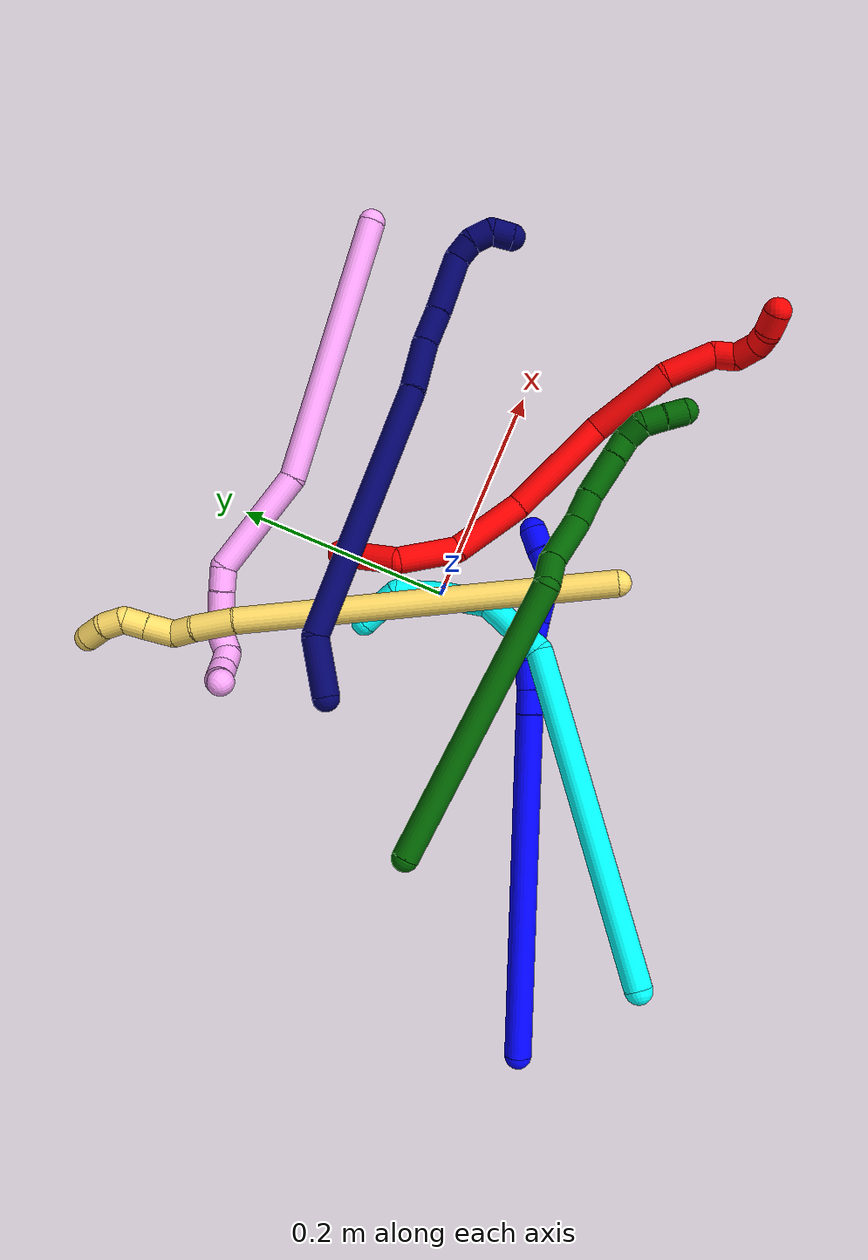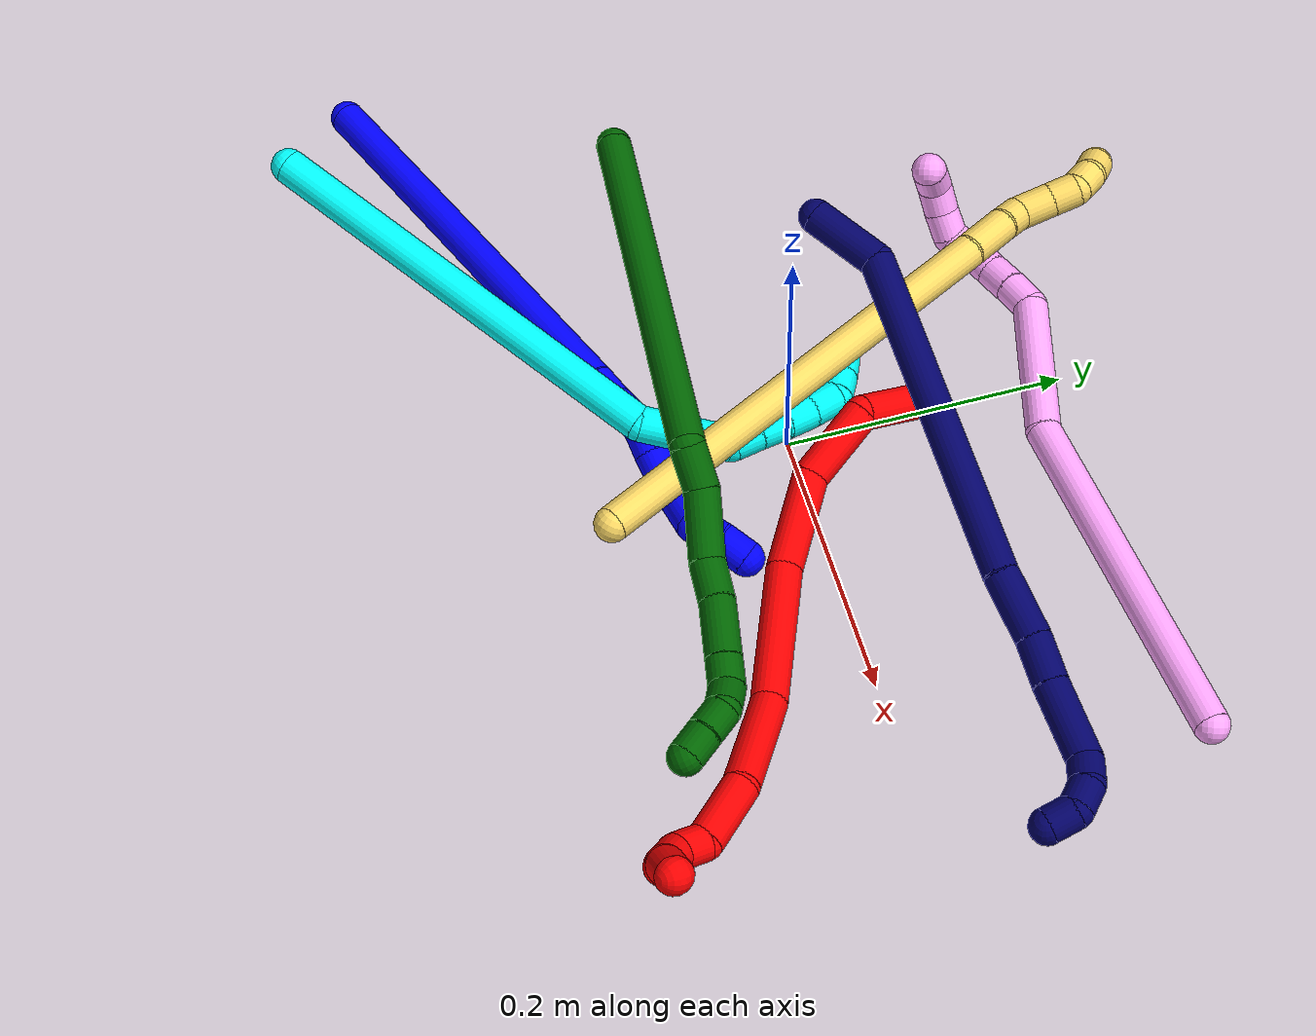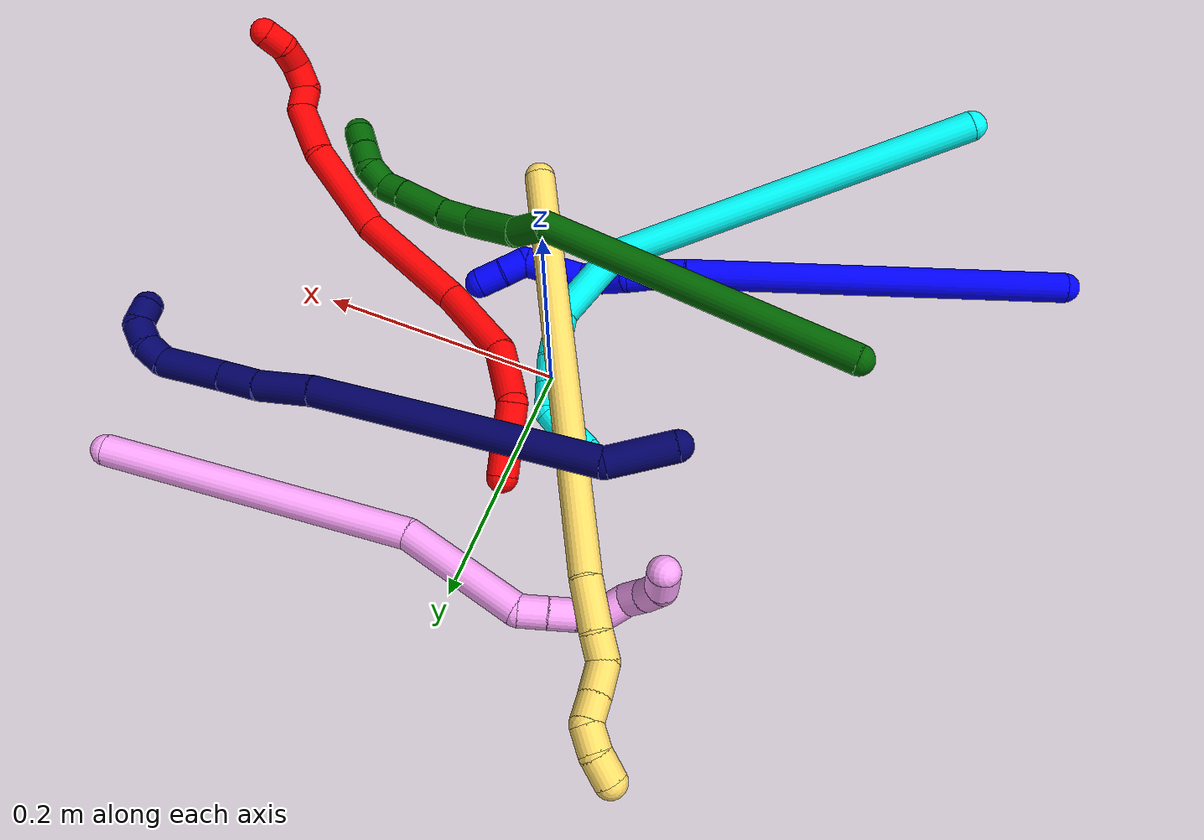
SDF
<sdf version="1.7">
 <world name="default">
  <plugin name="TubeGeneratorPlugin" filename="libtube_generator_plugin.so"/>
  <model name="photoneo_s_sensor">
   <static>1</static>
   <pose>0 0 2 1.57079 1.57079 3.14159</pose>
   <link name="link">
    <inertial><mass>0.1</mass></inertial>
    <sensor name="sensor" type="depth">
     <update_rate>30</update_rate>
     <camera>
      <horizontal_fov>1.22</horizontal_fov>
      <image><width>1920</width><height>1200</height><format>B8G8R8</format></image>
      <clip><near>0.1</near><far>4</far></clip>
      <depth_camera><output>points</output></depth_camera>
     </camera>
     <plugin name="camera_plugin" filename="libgazebo_ros_depth_camera.so">
      <baseline>0.2</baseline>
      <alwaysOn>1</alwaysOn>
      <updateRate>0.0</updateRate>
      <cameraName>camera_ir</cameraName>
      <imageTopicName>/camera/color/image_raw</imageTopicName>
      <cameraInfoTopicName>/camera/color/camera_info</cameraInfoTopicName>
      <depthImageTopicName>/camera/depth/image_raw</depthImageTopicName>
      <depthImageCameraInfoTopicName>/camera/depth/camera_info</depthImageCameraInfoTopicName>
      <pointCloudTopicName>/camera/depth/points</pointCloudTopicName>
      <frameName>fr_optical</frameName>
      <pointCloudCutoff>0.1</pointCloudCutoff>
      <pointCloudCutoffMax>2.0</pointCloudCutoffMax>
      <distortionK1>0</distortionK1>
      <distortionK2>0</distortionK2>
      <distortionK3>0</distortionK3>
      <distortionT1>0</distortionT1>
      <distortionT2>0</distortionT2>
      <CxPrime>0</CxPrime>
      <Cx>0</Cx>
      <Cy>0</Cy>
      <focalLength>0</focalLength>
      <hackBaseline>0</hackBaseline>
     </plugin>
    </sensor>
   </link>
  </model>
  <gravity>0 0 -9.8</gravity>
  <magnetic_field>6e-06 2.3e-05 -4.2e-05</magnetic_field>
  <atmosphere type="adiabatic"/>
  <physics name="default_physics" default="0" type="ode">
   <max_step_size>0.003</max_step_size>
   <real_time_factor>1</real_time_factor>
   <real_time_update_rate>1000</real_time_update_rate>
   <max_contacts>10000</max_contacts>
   <ode>
    <solver>
     <type>quick</type>
     <iters>100</iters>
     <sor>1.3</sor>
     <use_dynamic_moi_rescaling>0</use_dynamic_moi_rescaling>
    </solver>
    <constraints>
     <contact_max_correcting_vel>0</contact_max_correcting_vel>
     <contact_surface_layer>0.001</contact_surface_layer>
     <cfm>0</cfm>
     <erp>0.2</erp>
    </constraints>
   </ode>
  </physics>
  <scene><ambient>0.4 0.4 0.4 1</ambient><background>0.7 0.7 0.7 1</background><shadows>0</shadows></scene>
  <audio><device>default</device></audio>
  <spherical_coordinates>
   <surface_model>EARTH_WGS84</surface_model>
   <latitude_deg>0</latitude_deg>
   <longitude_deg>0</longitude_deg>
   <elevation>0</elevation>
   <heading_deg>0</heading_deg>
  </spherical_coordinates>
  <model name="bin">
   <static>1</static>
   <link name="bottom">
    <collision name="collision-bottom">
     <pose>0 0 -0.01 0 -0 0</pose>
     <geometry><box><size>0.8 0.6 0.02</size></box></geometry>
     <surface>
      <friction><ode><mu>100</mu><mu2>100</mu2></ode></friction>
      <contact><collide_bitmask>65535</collide_bitmask></contact>
     </surface>
    </collision>
   </link>
   <link name="west_wall">
    <collision name="collision-west_wall">
     <pose>-0.41 0 0.1 0 -0 0</pose>
     <geometry><box><size>0.02 0.6 0.2</size></box></geometry>
     <surface>
      <friction><ode><mu>100</mu><mu2>100</mu2></ode></friction>
      <contact><collide_bitmask>65535</collide_bitmask></contact>
     </surface>
    </collision>
   </link>
   <link name="east_wall">
    <collision name="collision-east_wall">
     <pose>0.41 0 0.1 0 -0 0</pose>
     <geometry><box><size>0.02 0.6 0.2</size></box></geometry>
     <surface>
      <friction><ode><mu>100</mu><mu2>100</mu2></ode></friction>
      <contact><collide_bitmask>65535</collide_bitmask></contact>
     </surface>
    </collision>
   </link>
   <link name="south_wall">
    <collision name="collision-south_wall">
     <pose>0 -0.31 0.1 0 -0 0</pose>
     <geometry><box><size>0.8 0.02 0.2</size></box></geometry>
     <surface>
      <friction><ode><mu>100</mu><mu2>100</mu2></ode></friction>
      <contact><collide_bitmask>65535</collide_bitmask></contact>
     </surface>
    </collision>
   </link>
   <link name="north_wall">
    <collision name="collision-north_wall">
     <pose>0 0.31 0.1 0 -0 0</pose>
     <geometry><box><size>0.8 0.02 0.2</size></box></geometry>
     <surface>
      <friction><ode><mu>100</mu><mu2>100</mu2></ode></friction>
      <contact><collide_bitmask>65535</collide_bitmask></contact>
     </surface>
    </collision>
   </link>
  </model>
  <model name="1">
   <static>0</static>
   <link name="1">
    <collision name="collision-cylinder-e_1_1_4">
     <pose>0.111933 0.013942 -0.113052 -3.01889 0.77665 -2.8435</pose>
     <geometry><cylinder><radius>0.0125</radius><length>0.319401</length></cylinder></geometry>
     <surface>
      <friction><ode><mu>1.16</mu><mu2>1.16</mu2><slip1>0</slip1><slip2>0</slip2></ode></friction>
      <contact><ode><kp>1e+06</kp><kd>1</kd><max_vel>0</max_vel><min_depth>0.001</min_depth></ode></contact>
     </surface>
    </collision>
    <visual name="visual-cylinder-e_1_1_4">
     <pose>0.111933 0.013942 -0.113052 -3.01889 0.77665 -2.8435</pose>
     <geometry><cylinder><radius>0.0125</radius><length>0.319401</length></cylinder></geometry>
     <material><ambient>0 0 1 1</ambient></material>
    </visual>
    <collision name="collision-cylinder-e_2_4_5">
     <pose>0.230928 0.028661 -0.234606 -3.05051 0.691139 -2.88977</pose>
     <geometry><cylinder><radius>0.0125</radius><length>0.022156</length></cylinder></geometry>
     <surface>
      <friction><ode><mu>1.16</mu><mu2>1.16</mu2><slip1>0</slip1><slip2>0</slip2></ode></friction>
      <contact><ode><kp>1e+06</kp><kd>1</kd><max_vel>0</max_vel><min_depth>0.001</min_depth></ode></contact>
     </surface>
    </collision>
    <visual name="visual-cylinder-e_2_4_5">
     <pose>0.230928 0.028661 -0.234606 -3.05051 0.691139 -2.88977</pose>
     <geometry><cylinder><radius>0.0125</radius><length>0.022156</length></cylinder></geometry>
     <material><ambient>0 0 1 1</ambient></material>
    </visual>
    <collision name="collision-cylinder-e_3_5_6">
     <pose>0.246068 0.031459 -0.253748 -2.95386 0.640815 -2.58871</pose>
     <geometry><cylinder><radius>0.0125</radius><length>0.027026</length></cylinder></geometry>
     <surface>
      <friction><ode><mu>1.16</mu><mu2>1.16</mu2><slip1>0</slip1><slip2>0</slip2></ode></friction>
      <contact><ode><kp>1e+06</kp><kd>1</kd><max_vel>0</max_vel><min_depth>0.001</min_depth></ode></contact>
     </surface>
    </collision>
    <visual name="visual-cylinder-e_3_5_6">
     <pose>0.246068 0.031459 -0.253748 -2.95386 0.640815 -2.58871</pose>
     <geometry><cylinder><radius>0.0125</radius><length>0.027026</length></cylinder></geometry>
     <material><ambient>0 0 1 1</ambient></material>
    </visual>
    <collision name="collision-cylinder-e_4_6_7">
     <pose>0.257606 0.031573 -0.273804 2.94171 0.345699 2.09891</pose>
     <geometry><cylinder><radius>0.0125</radius><length>0.020418</length></cylinder></geometry>
     <surface>
      <friction><ode><mu>1.16</mu><mu2>1.16</mu2><slip1>0</slip1><slip2>0</slip2></ode></friction>
      <contact><ode><kp>1e+06</kp><kd>1</kd><max_vel>0</max_vel><min_depth>0.001</min_depth></ode></contact>
     </surface>
    </collision>
    <visual name="visual-cylinder-e_4_6_7">
     <pose>0.257606 0.031573 -0.273804 2.94171 0.345699 2.09891</pose>
     <geometry><cylinder><radius>0.0125</radius><length>0.020418</length></cylinder></geometry>
     <material><ambient>0 0 1 1</ambient></material>
    </visual>
    <collision name="collision-cylinder-e_5_7_8">
     <pose>0.266191 0.028024 -0.291838 2.9533 0.528587 2.47016</pose>
     <geometry><cylinder><radius>0.0125</radius><length>0.020325</length></cylinder></geometry>
     <surface>
      <friction><ode><mu>1.16</mu><mu2>1.16</mu2><slip1>0</slip1><slip2>0</slip2></ode></friction>
      <contact><ode><kp>1e+06</kp><kd>1</kd><max_vel>0</max_vel><min_depth>0.001</min_depth></ode></contact>
     </surface>
    </collision>
    <visual name="visual-cylinder-e_5_7_8">
     <pose>0.266191 0.028024 -0.291838 2.9533 0.528587 2.47016</pose>
     <geometry><cylinder><radius>0.0125</radius><length>0.020325</length></cylinder></geometry>
     <material><ambient>0 0 1 1</ambient></material>
    </visual>
    <collision name="collision-cylinder-e_6_8_9">
     <pose>0.280686 0.025397 -0.306975 2.99174 0.95786 2.85444</pose>
     <geometry><cylinder><radius>0.0125</radius><length>0.022911</length></cylinder></geometry>
     <surface>
      <friction><ode><mu>1.16</mu><mu2>1.16</mu2><slip1>0</slip1><slip2>0</slip2></ode></friction>
      <contact><ode><kp>1e+06</kp><kd>1</kd><max_vel>0</max_vel><min_depth>0.001</min_depth></ode></contact>
     </surface>
    </collision>
    <visual name="visual-cylinder-e_6_8_9">
     <pose>0.280686 0.025397 -0.306975 2.99174 0.95786 2.85444</pose>
     <geometry><cylinder><radius>0.0125</radius><length>0.022911</length></cylinder></geometry>
     <material><ambient>0 0 1 1</ambient></material>
    </visual>
    <collision name="collision-cylinder-e_7_9_10">
     <pose>0.300568 0.02331 -0.320801 2.9918 0.957857 2.85456</pose>
     <geometry><cylinder><radius>0.0125</radius><length>0.025703</length></cylinder></geometry>
     <surface>
      <friction><ode><mu>1.16</mu><mu2>1.16</mu2><slip1>0</slip1><slip2>0</slip2></ode></friction>
      <contact><ode><kp>1e+06</kp><kd>1</kd><max_vel>0</max_vel><min_depth>0.001</min_depth></ode></contact>
     </surface>
    </collision>
    <visual name="visual-cylinder-e_7_9_10">
     <pose>0.300568 0.02331 -0.320801 2.9918 0.957857 2.85456</pose>
     <geometry><cylinder><radius>0.0125</radius><length>0.025703</length></cylinder></geometry>
     <material><ambient>0 0 1 1</ambient></material>
    </visual>
    <collision name="collision-cylinder-e_8_10_11">
     <pose>0.315127 0.026788 -0.336513 -2.64242 0.400139 -1.34402</pose>
     <geometry><cylinder><radius>0.0125</radius><length>0.020781</length></cylinder></geometry>
     <surface>
      <friction><ode><mu>1.16</mu><mu2>1.16</mu2><slip1>0</slip1><slip2>0</slip2></ode></friction>
      <contact><ode><kp>1e+06</kp><kd>1</kd><max_vel>0</max_vel><min_depth>0.001</min_depth></ode></contact>
     </surface>
    </collision>
    <visual name="visual-cylinder-e_8_10_11">
     <pose>0.315127 0.026788 -0.336513 -2.64242 0.400139 -1.34402</pose>
     <geometry><cylinder><radius>0.0125</radius><length>0.020781</length></cylinder></geometry>
     <material><ambient>0 0 1 1</ambient></material>
    </visual>
    <collision name="collision-cylinder-e_9_11_2">
     <pose>0.32285 0.034928 -0.354243 -2.77703 0.352669 -1.53692</pose>
     <geometry><cylinder><radius>0.0125</radius><length>0.021279</length></cylinder></geometry>
     <surface>
      <friction><ode><mu>1.16</mu><mu2>1.16</mu2><slip1>0</slip1><slip2>0</slip2></ode></friction>
      <contact><ode><kp>1e+06</kp><kd>1</kd><max_vel>0</max_vel><min_depth>0.001</min_depth></ode></contact>
     </surface>
    </collision>
    <visual name="visual-cylinder-e_9_11_2">
     <pose>0.32285 0.034928 -0.354243 -2.77703 0.352669 -1.53692</pose>
     <geometry><cylinder><radius>0.0125</radius><length>0.021279</length></cylinder></geometry>
     <material><ambient>0 0 1 1</ambient></material>
    </visual>
    <collision name="collision-sphere-2">
     <pose>0.326525 0.038488 -0.363572 0 -0 0</pose>
     <geometry><sphere><radius>0.0125</radius></sphere></geometry>
     <surface>
      <friction><ode><mu>1.16</mu><mu2>1.16</mu2><slip1>0</slip1><slip2>0</slip2></ode></friction>
      <contact><ode><kp>1e+06</kp><kd>1</kd><max_vel>0</max_vel><min_depth>0.001</min_depth></ode></contact>
     </surface>
    </collision>
    <visual name="visual-sphere-2">
     <pose>0.326525 0.038488 -0.363572 0 -0 0</pose>
     <geometry><sphere><radius>0.0125</radius></sphere></geometry>
     <material><ambient>0 0 1 1</ambient></material>
    </visual>
    <collision name="collision-sphere-11">
     <pose>0.319175 0.031369 -0.344915 0 -0 0</pose>
     <geometry><sphere><radius>0.0125</radius></sphere></geometry>
     <surface>
      <friction><ode><mu>1.16</mu><mu2>1.16</mu2><slip1>0</slip1><slip2>0</slip2></ode></friction>
      <contact><ode><kp>1e+06</kp><kd>1</kd><max_vel>0</max_vel><min_depth>0.001</min_depth></ode></contact>
     </surface>
    </collision>
    <visual name="visual-sphere-11">
     <pose>0.319175 0.031369 -0.344915 0 -0 0</pose>
     <geometry><sphere><radius>0.0125</radius></sphere></geometry>
     <material><ambient>0 0 1 1</ambient></material>
    </visual>
    <collision name="collision-sphere-10">
     <pose>0.31108 0.022207 -0.328111 0 -0 0</pose>
     <geometry><sphere><radius>0.0125</radius></sphere></geometry>
     <surface>
      <friction><ode><mu>1.16</mu><mu2>1.16</mu2><slip1>0</slip1><slip2>0</slip2></ode></friction>
      <contact><ode><kp>1e+06</kp><kd>1</kd><max_vel>0</max_vel><min_depth>0.001</min_depth></ode></contact>
     </surface>
    </collision>
    <visual name="visual-sphere-10">
     <pose>0.31108 0.022207 -0.328111 0 -0 0</pose>
     <geometry><sphere><radius>0.0125</radius></sphere></geometry>
     <material><ambient>0 0 1 1</ambient></material>
    </visual>
    <collision name="collision-sphere-9">
     <pose>0.290056 0.024413 -0.313491 0 -0 0</pose>
     <geometry><sphere><radius>0.0125</radius></sphere></geometry>
     <surface>
      <friction><ode><mu>1.16</mu><mu2>1.16</mu2><slip1>0</slip1><slip2>0</slip2></ode></friction>
      <contact><ode><kp>1e+06</kp><kd>1</kd><max_vel>0</max_vel><min_depth>0.001</min_depth></ode></contact>
     </surface>
    </collision>
    <visual name="visual-sphere-9">
     <pose>0.290056 0.024413 -0.313491 0 -0 0</pose>
     <geometry><sphere><radius>0.0125</radius></sphere></geometry>
     <material><ambient>0 0 1 1</ambient></material>
    </visual>
    <collision name="collision-sphere-4">
     <pose>0.223867 0.027885 -0.226105 0 -0 0</pose>
     <geometry><sphere><radius>0.0125</radius></sphere></geometry>
     <surface>
      <friction><ode><mu>1.16</mu><mu2>1.16</mu2><slip1>0</slip1><slip2>0</slip2></ode></friction>
      <contact><ode><kp>1e+06</kp><kd>1</kd><max_vel>0</max_vel><min_depth>0.001</min_depth></ode></contact>
     </surface>
    </collision>
    <visual name="visual-sphere-4">
     <pose>0.223867 0.027885 -0.226105 0 -0 0</pose>
     <geometry><sphere><radius>0.0125</radius></sphere></geometry>
     <material><ambient>0 0 1 1</ambient></material>
    </visual>
    <collision name="collision-sphere-1">
     <geometry><sphere><radius>0.0125</radius></sphere></geometry>
     <surface>
      <friction><ode><mu>1.16</mu><mu2>1.16</mu2><slip1>0</slip1><slip2>0</slip2></ode></friction>
      <contact><ode><kp>1e+06</kp><kd>1</kd><max_vel>0</max_vel><min_depth>0.001</min_depth></ode></contact>
     </surface>
    </collision>
    <visual name="visual-sphere-1">
     <geometry><sphere><radius>0.0125</radius></sphere></geometry>
     <material><ambient>0 0 1 1</ambient></material>
    </visual>
    <collision name="collision-sphere-8">
     <pose>0.271316 0.026381 -0.300458 0 -0 0</pose>
     <geometry><sphere><radius>0.0125</radius></sphere></geometry>
     <surface>
      <friction><ode><mu>1.16</mu><mu2>1.16</mu2><slip1>0</slip1><slip2>0</slip2></ode></friction>
      <contact><ode><kp>1e+06</kp><kd>1</kd><max_vel>0</max_vel><min_depth>0.001</min_depth></ode></contact>
     </surface>
    </collision>
    <visual name="visual-sphere-8">
     <pose>0.271316 0.026381 -0.300458 0 -0 0</pose>
     <geometry><sphere><radius>0.0125</radius></sphere></geometry>
     <material><ambient>0 0 1 1</ambient></material>
    </visual>
    <collision name="collision-sphere-5">
     <pose>0.237989 0.029437 -0.243106 0 -0 0</pose>
     <geometry><sphere><radius>0.0125</radius></sphere></geometry>
     <surface>
      <friction><ode><mu>1.16</mu><mu2>1.16</mu2><slip1>0</slip1><slip2>0</slip2></ode></friction>
      <contact><ode><kp>1e+06</kp><kd>1</kd><max_vel>0</max_vel><min_depth>0.001</min_depth></ode></contact>
     </surface>
    </collision>
    <visual name="visual-sphere-5">
     <pose>0.237989 0.029437 -0.243106 0 -0 0</pose>
     <geometry><sphere><radius>0.0125</radius></sphere></geometry>
     <material><ambient>0 0 1 1</ambient></material>
    </visual>
    <collision name="collision-sphere-6">
     <pose>0.254147 0.033481 -0.26439 0 -0 0</pose>
     <geometry><sphere><radius>0.0125</radius></sphere></geometry>
     <surface>
      <friction><ode><mu>1.16</mu><mu2>1.16</mu2><slip1>0</slip1><slip2>0</slip2></ode></friction>
      <contact><ode><kp>1e+06</kp><kd>1</kd><max_vel>0</max_vel><min_depth>0.001</min_depth></ode></contact>
     </surface>
    </collision>
    <visual name="visual-sphere-6">
     <pose>0.254147 0.033481 -0.26439 0 -0 0</pose>
     <geometry><sphere><radius>0.0125</radius></sphere></geometry>
     <material><ambient>0 0 1 1</ambient></material>
    </visual>
    <collision name="collision-sphere-7">
     <pose>0.261066 0.029666 -0.283218 0 -0 0</pose>
     <geometry><sphere><radius>0.0125</radius></sphere></geometry>
     <surface>
      <friction><ode><mu>1.16</mu><mu2>1.16</mu2><slip1>0</slip1><slip2>0</slip2></ode></friction>
      <contact><ode><kp>1e+06</kp><kd>1</kd><max_vel>0</max_vel><min_depth>0.001</min_depth></ode></contact>
     </surface>
    </collision>
    <visual name="visual-sphere-7">
     <pose>0.261066 0.029666 -0.283218 0 -0 0</pose>
     <geometry><sphere><radius>0.0125</radius></sphere></geometry>
     <material><ambient>0 0 1 1</ambient></material>
    </visual>
    <inertial>
     <pose>0.171526 0.019267 -0.178993 0 -0 0</pose>
     <mass>0.5</mass>
     <inertia>
      <ixx>-0.002414</ixx>
      <ixy>0</ixy>
      <ixz>0</ixz>
      <iyy>0.002097</iyy>
      <iyz>0</iyz>
      <izz>-0.002188</izz>
     </inertia>
    </inertial>
   </link>
   <pose>-0.368691 -0.23302 0.011497 0.285654 -0.802692 0.081527</pose>
  </model>
  <model name="2">
   <static>0</static>
   <link name="2">
    <collision name="collision-cylinder-e_1_1_4">
     <pose>-0.001656 0.001019 0.028916 -0.035209 -0.057168 0.001007</pose>
     <geometry><cylinder><radius>0.0125</radius><length>0.057963</length></cylinder></geometry>
     <surface>
      <friction><ode><mu>1.16</mu><mu2>1.16</mu2><slip1>0</slip1><slip2>0</slip2></ode></friction>
      <contact><ode><kp>1e+06</kp><kd>1</kd><max_vel>0</max_vel><min_depth>0.001</min_depth></ode></contact>
     </surface>
    </collision>
    <visual name="visual-cylinder-e_1_1_4">
     <pose>-0.001656 0.001019 0.028916 -0.035209 -0.057168 0.001007</pose>
     <geometry><cylinder><radius>0.0125</radius><length>0.057963</length></cylinder></geometry>
     <material><ambient>1 0 0 1</ambient></material>
    </visual>
    <collision name="collision-cylinder-e_2_4_5">
     <pose>-0.003326 -0.016285 0.080387 0.682206 -0.000497 -0.000176</pose>
     <geometry><cylinder><radius>0.0125</radius><length>0.058118</length></cylinder></geometry>
     <surface>
      <friction><ode><mu>1.16</mu><mu2>1.16</mu2><slip1>0</slip1><slip2>0</slip2></ode></friction>
      <contact><ode><kp>1e+06</kp><kd>1</kd><max_vel>0</max_vel><min_depth>0.001</min_depth></ode></contact>
     </surface>
    </collision>
    <visual name="visual-cylinder-e_2_4_5">
     <pose>-0.003326 -0.016285 0.080387 0.682206 -0.000497 -0.000176</pose>
     <geometry><cylinder><radius>0.0125</radius><length>0.058118</length></cylinder></geometry>
     <material><ambient>1 0 0 1</ambient></material>
    </visual>
    <collision name="collision-cylinder-e_3_5_6">
     <pose>0.011433 -0.057388 0.126211 0.774822 0.425922 0.17601</pose>
     <geometry><cylinder><radius>0.0125</radius><length>0.071518</length></cylinder></geometry>
     <surface>
      <friction><ode><mu>1.16</mu><mu2>1.16</mu2><slip1>0</slip1><slip2>0</slip2></ode></friction>
      <contact><ode><kp>1e+06</kp><kd>1</kd><max_vel>0</max_vel><min_depth>0.001</min_depth></ode></contact>
     </surface>
    </collision>
    <visual name="visual-cylinder-e_3_5_6">
     <pose>0.011433 -0.057388 0.126211 0.774822 0.425922 0.17601</pose>
     <geometry><cylinder><radius>0.0125</radius><length>0.071518</length></cylinder></geometry>
     <material><ambient>1 0 0 1</ambient></material>
    </visual>
    <collision name="collision-cylinder-e_4_6_7">
     <pose>0.056091 -0.108181 0.180338 0.737078 0.622075 0.24703</pose>
     <geometry><cylinder><radius>0.0125</radius><length>0.102567</length></cylinder></geometry>
     <surface>
      <friction><ode><mu>1.16</mu><mu2>1.16</mu2><slip1>0</slip1><slip2>0</slip2></ode></friction>
      <contact><ode><kp>1e+06</kp><kd>1</kd><max_vel>0</max_vel><min_depth>0.001</min_depth></ode></contact>
     </surface>
    </collision>
    <visual name="visual-cylinder-e_4_6_7">
     <pose>0.056091 -0.108181 0.180338 0.737078 0.622075 0.24703</pose>
     <geometry><cylinder><radius>0.0125</radius><length>0.102567</length></cylinder></geometry>
     <material><ambient>1 0 0 1</ambient></material>
    </visual>
    <collision name="collision-cylinder-e_5_7_8">
     <pose>0.109058 -0.145863 0.241978 0.304396 0.620983 0.098353</pose>
     <geometry><cylinder><radius>0.0125</radius><length>0.079343</length></cylinder></geometry>
     <surface>
      <friction><ode><mu>1.16</mu><mu2>1.16</mu2><slip1>0</slip1><slip2>0</slip2></ode></friction>
      <contact><ode><kp>1e+06</kp><kd>1</kd><max_vel>0</max_vel><min_depth>0.001</min_depth></ode></contact>
     </surface>
    </collision>
    <visual name="visual-cylinder-e_5_7_8">
     <pose>0.109058 -0.145863 0.241978 0.304396 0.620983 0.098353</pose>
     <geometry><cylinder><radius>0.0125</radius><length>0.079343</length></cylinder></geometry>
     <material><ambient>1 0 0 1</ambient></material>
    </visual>
    <collision name="collision-cylinder-e_6_8_9">
     <pose>0.139473 -0.164969 0.293225 0.431981 0.314619 0.069579</pose>
     <geometry><cylinder><radius>0.0125</radius><length>0.047396</length></cylinder></geometry>
     <surface>
      <friction><ode><mu>1.16</mu><mu2>1.16</mu2><slip1>0</slip1><slip2>0</slip2></ode></friction>
      <contact><ode><kp>1e+06</kp><kd>1</kd><max_vel>0</max_vel><min_depth>0.001</min_depth></ode></contact>
     </surface>
    </collision>
    <visual name="visual-cylinder-e_6_8_9">
     <pose>0.139473 -0.164969 0.293225 0.431981 0.314619 0.069579</pose>
     <geometry><cylinder><radius>0.0125</radius><length>0.047396</length></cylinder></geometry>
     <material><ambient>1 0 0 1</ambient></material>
    </visual>
    <collision name="collision-cylinder-e_7_9_10">
     <pose>0.145511 -0.175029 0.323662 0.062618 -0.128995 -0.004046</pose>
     <geometry><cylinder><radius>0.0125</radius><length>0.020151</length></cylinder></geometry>
     <surface>
      <friction><ode><mu>1.16</mu><mu2>1.16</mu2><slip1>0</slip1><slip2>0</slip2></ode></friction>
      <contact><ode><kp>1e+06</kp><kd>1</kd><max_vel>0</max_vel><min_depth>0.001</min_depth></ode></contact>
     </surface>
    </collision>
    <visual name="visual-cylinder-e_7_9_10">
     <pose>0.145511 -0.175029 0.323662 0.062618 -0.128995 -0.004046</pose>
     <geometry><cylinder><radius>0.0125</radius><length>0.020151</length></cylinder></geometry>
     <material><ambient>1 0 0 1</ambient></material>
    </visual>
    <collision name="collision-cylinder-e_8_10_11">
     <pose>0.14977 -0.174624 0.343304 -0.106087 0.518986 -0.028188</pose>
     <geometry><cylinder><radius>0.0125</radius><length>0.0224</length></cylinder></geometry>
     <surface>
      <friction><ode><mu>1.16</mu><mu2>1.16</mu2><slip1>0</slip1><slip2>0</slip2></ode></friction>
      <contact><ode><kp>1e+06</kp><kd>1</kd><max_vel>0</max_vel><min_depth>0.001</min_depth></ode></contact>
     </surface>
    </collision>
    <visual name="visual-cylinder-e_8_10_11">
     <pose>0.14977 -0.174624 0.343304 -0.106087 0.518986 -0.028188</pose>
     <geometry><cylinder><radius>0.0125</radius><length>0.0224</length></cylinder></geometry>
     <material><ambient>1 0 0 1</ambient></material>
    </visual>
    <collision name="collision-cylinder-e_9_11_12">
     <pose>0.162188 -0.167761 0.357911 -0.868477 0.731763 -0.351693</pose>
     <geometry><cylinder><radius>0.0125</radius><length>0.020543</length></cylinder></geometry>
     <surface>
      <friction><ode><mu>1.16</mu><mu2>1.16</mu2><slip1>0</slip1><slip2>0</slip2></ode></friction>
      <contact><ode><kp>1e+06</kp><kd>1</kd><max_vel>0</max_vel><min_depth>0.001</min_depth></ode></contact>
     </surface>
    </collision>
    <visual name="visual-cylinder-e_9_11_12">
     <pose>0.162188 -0.167761 0.357911 -0.868477 0.731763 -0.351693</pose>
     <geometry><cylinder><radius>0.0125</radius><length>0.020543</length></cylinder></geometry>
     <material><ambient>1 0 0 1</ambient></material>
    </visual>
    <collision name="collision-cylinder-e_10_12_2">
     <pose>0.17804 -0.159955 0.366766 -0.466342 1.11681 -0.294585</pose>
     <geometry><cylinder><radius>0.0125</radius><length>0.020003</length></cylinder></geometry>
     <surface>
      <friction><ode><mu>1.16</mu><mu2>1.16</mu2><slip1>0</slip1><slip2>0</slip2></ode></friction>
      <contact><ode><kp>1e+06</kp><kd>1</kd><max_vel>0</max_vel><min_depth>0.001</min_depth></ode></contact>
     </surface>
    </collision>
    <visual name="visual-cylinder-e_10_12_2">
     <pose>0.17804 -0.159955 0.366766 -0.466342 1.11681 -0.294585</pose>
     <geometry><cylinder><radius>0.0125</radius><length>0.020003</length></cylinder></geometry>
     <material><ambient>1 0 0 1</ambient></material>
    </visual>
    <collision name="collision-sphere-2">
     <pose>0.187028 -0.157983 0.370684 0 -0 0</pose>
     <geometry><sphere><radius>0.0125</radius></sphere></geometry>
     <surface>
      <friction><ode><mu>1.16</mu><mu2>1.16</mu2><slip1>0</slip1><slip2>0</slip2></ode></friction>
      <contact><ode><kp>1e+06</kp><kd>1</kd><max_vel>0</max_vel><min_depth>0.001</min_depth></ode></contact>
     </surface>
    </collision>
    <visual name="visual-sphere-2">
     <pose>0.187028 -0.157983 0.370684 0 -0 0</pose>
     <geometry><sphere><radius>0.0125</radius></sphere></geometry>
     <material><ambient>1 0 0 1</ambient></material>
    </visual>
    <collision name="collision-sphere-12">
     <pose>0.169052 -0.161927 0.362848 0 -0 0</pose>
     <geometry><sphere><radius>0.0125</radius></sphere></geometry>
     <surface>
      <friction><ode><mu>1.16</mu><mu2>1.16</mu2><slip1>0</slip1><slip2>0</slip2></ode></friction>
      <contact><ode><kp>1e+06</kp><kd>1</kd><max_vel>0</max_vel><min_depth>0.001</min_depth></ode></contact>
     </surface>
    </collision>
    <visual name="visual-sphere-12">
     <pose>0.169052 -0.161927 0.362848 0 -0 0</pose>
     <geometry><sphere><radius>0.0125</radius></sphere></geometry>
     <material><ambient>1 0 0 1</ambient></material>
    </visual>
    <collision name="collision-sphere-11">
     <pose>0.155325 -0.173594 0.352975 0 -0 0</pose>
     <geometry><sphere><radius>0.0125</radius></sphere></geometry>
     <surface>
      <friction><ode><mu>1.16</mu><mu2>1.16</mu2><slip1>0</slip1><slip2>0</slip2></ode></friction>
      <contact><ode><kp>1e+06</kp><kd>1</kd><max_vel>0</max_vel><min_depth>0.001</min_depth></ode></contact>
     </surface>
    </collision>
    <visual name="visual-sphere-11">
     <pose>0.155325 -0.173594 0.352975 0 -0 0</pose>
     <geometry><sphere><radius>0.0125</radius></sphere></geometry>
     <material><ambient>1 0 0 1</ambient></material>
    </visual>
    <collision name="collision-sphere-10">
     <pose>0.144215 -0.175654 0.333634 0 -0 0</pose>
     <geometry><sphere><radius>0.0125</radius></sphere></geometry>
     <surface>
      <friction><ode><mu>1.16</mu><mu2>1.16</mu2><slip1>0</slip1><slip2>0</slip2></ode></friction>
      <contact><ode><kp>1e+06</kp><kd>1</kd><max_vel>0</max_vel><min_depth>0.001</min_depth></ode></contact>
     </surface>
    </collision>
    <visual name="visual-sphere-10">
     <pose>0.144215 -0.175654 0.333634 0 -0 0</pose>
     <geometry><sphere><radius>0.0125</radius></sphere></geometry>
     <material><ambient>1 0 0 1</ambient></material>
    </visual>
    <collision name="collision-sphere-9">
     <pose>0.146807 -0.174403 0.31369 0 -0 0</pose>
     <geometry><sphere><radius>0.0125</radius></sphere></geometry>
     <surface>
      <friction><ode><mu>1.16</mu><mu2>1.16</mu2><slip1>0</slip1><slip2>0</slip2></ode></friction>
      <contact><ode><kp>1e+06</kp><kd>1</kd><max_vel>0</max_vel><min_depth>0.001</min_depth></ode></contact>
     </surface>
    </collision>
    <visual name="visual-sphere-9">
     <pose>0.146807 -0.174403 0.31369 0 -0 0</pose>
     <geometry><sphere><radius>0.0125</radius></sphere></geometry>
     <material><ambient>1 0 0 1</ambient></material>
    </visual>
    <collision name="collision-sphere-4">
     <pose>-0.003312 0.002037 0.057832 0 -0 0</pose>
     <geometry><sphere><radius>0.0125</radius></sphere></geometry>
     <surface>
      <friction><ode><mu>1.16</mu><mu2>1.16</mu2><slip1>0</slip1><slip2>0</slip2></ode></friction>
      <contact><ode><kp>1e+06</kp><kd>1</kd><max_vel>0</max_vel><min_depth>0.001</min_depth></ode></contact>
     </surface>
    </collision>
    <visual name="visual-sphere-4">
     <pose>-0.003312 0.002037 0.057832 0 -0 0</pose>
     <geometry><sphere><radius>0.0125</radius></sphere></geometry>
     <material><ambient>1 0 0 1</ambient></material>
    </visual>
    <collision name="collision-sphere-1">
     <geometry><sphere><radius>0.0125</radius></sphere></geometry>
     <surface>
      <friction><ode><mu>1.16</mu><mu2>1.16</mu2><slip1>0</slip1><slip2>0</slip2></ode></friction>
      <contact><ode><kp>1e+06</kp><kd>1</kd><max_vel>0</max_vel><min_depth>0.001</min_depth></ode></contact>
     </surface>
    </collision>
    <visual name="visual-sphere-1">
     <geometry><sphere><radius>0.0125</radius></sphere></geometry>
     <material><ambient>1 0 0 1</ambient></material>
    </visual>
    <collision name="collision-sphere-8">
     <pose>0.13214 -0.155534 0.27276 0 -0 0</pose>
     <geometry><sphere><radius>0.0125</radius></sphere></geometry>
     <surface>
      <friction><ode><mu>1.16</mu><mu2>1.16</mu2><slip1>0</slip1><slip2>0</slip2></ode></friction>
      <contact><ode><kp>1e+06</kp><kd>1</kd><max_vel>0</max_vel><min_depth>0.001</min_depth></ode></contact>
     </surface>
    </collision>
    <visual name="visual-sphere-8">
     <pose>0.13214 -0.155534 0.27276 0 -0 0</pose>
     <geometry><sphere><radius>0.0125</radius></sphere></geometry>
     <material><ambient>1 0 0 1</ambient></material>
    </visual>
    <collision name="collision-sphere-5">
     <pose>-0.003341 -0.034606 0.102942 0 -0 0</pose>
     <geometry><sphere><radius>0.0125</radius></sphere></geometry>
     <surface>
      <friction><ode><mu>1.16</mu><mu2>1.16</mu2><slip1>0</slip1><slip2>0</slip2></ode></friction>
      <contact><ode><kp>1e+06</kp><kd>1</kd><max_vel>0</max_vel><min_depth>0.001</min_depth></ode></contact>
     </surface>
    </collision>
    <visual name="visual-sphere-5">
     <pose>-0.003341 -0.034606 0.102942 0 -0 0</pose>
     <geometry><sphere><radius>0.0125</radius></sphere></geometry>
     <material><ambient>1 0 0 1</ambient></material>
    </visual>
    <collision name="collision-sphere-6">
     <pose>0.026208 -0.080169 0.149479 0 -0 0</pose>
     <geometry><sphere><radius>0.0125</radius></sphere></geometry>
     <surface>
      <friction><ode><mu>1.16</mu><mu2>1.16</mu2><slip1>0</slip1><slip2>0</slip2></ode></friction>
      <contact><ode><kp>1e+06</kp><kd>1</kd><max_vel>0</max_vel><min_depth>0.001</min_depth></ode></contact>
     </surface>
    </collision>
    <visual name="visual-sphere-6">
     <pose>0.026208 -0.080169 0.149479 0 -0 0</pose>
     <geometry><sphere><radius>0.0125</radius></sphere></geometry>
     <material><ambient>1 0 0 1</ambient></material>
    </visual>
    <collision name="collision-sphere-7">
     <pose>0.085975 -0.136193 0.211196 0 -0 0</pose>
     <geometry><sphere><radius>0.0125</radius></sphere></geometry>
     <surface>
      <friction><ode><mu>1.16</mu><mu2>1.16</mu2><slip1>0</slip1><slip2>0</slip2></ode></friction>
      <contact><ode><kp>1e+06</kp><kd>1</kd><max_vel>0</max_vel><min_depth>0.001</min_depth></ode></contact>
     </surface>
    </collision>
    <visual name="visual-sphere-7">
     <pose>0.085975 -0.136193 0.211196 0 -0 0</pose>
     <geometry><sphere><radius>0.0125</radius></sphere></geometry>
     <material><ambient>1 0 0 1</ambient></material>
    </visual>
    <inertial>
     <pose>0.06945 -0.099128 0.191738 0 -0 0</pose>
     <mass>0.5</mass>
     <inertia>
      <ixx>0.000234</ixx>
      <ixy>0</ixy>
      <ixz>0</ixz>
      <iyy>0.000209</iyy>
      <iyz>0</iyz>
      <izz>2.7e-05</izz>
     </inertia>
    </inertial>
   </link>
   <pose>-0.001333 0.101241 0.012499 1.15257 -0.412148 0.491102</pose>
  </model>
  <model name="3">
   <static>0</static>
   <link name="3">
    <collision name="collision-cylinder-e_1_1_4">
     <pose>0.025589 0.005516 -0.151489 -3.1052 0.167225 -2.71391</pose>
     <geometry><cylinder><radius>0.0125</radius><length>0.307468</length></cylinder></geometry>
     <surface>
      <friction><ode><mu>1.16</mu><mu2>1.16</mu2><slip1>0</slip1><slip2>0</slip2></ode></friction>
      <contact><ode><kp>1e+06</kp><kd>1</kd><max_vel>0</max_vel><min_depth>0.001</min_depth></ode></contact>
     </surface>
    </collision>
    <visual name="visual-cylinder-e_1_1_4">
     <pose>0.025589 0.005516 -0.151489 -3.1052 0.167225 -2.71391</pose>
     <geometry><cylinder><radius>0.0125</radius><length>0.307468</length></cylinder></geometry>
     <material><ambient>0.003922 1 0.996078 1</ambient></material>
    </visual>
    <collision name="collision-cylinder-e_2_4_5">
     <pose>0.052653 0.028195 -0.330702 -2.58725 0.045222 -0.158651</pose>
     <geometry><cylinder><radius>0.0125</radius><length>0.065279</length></cylinder></geometry>
     <surface>
      <friction><ode><mu>1.16</mu><mu2>1.16</mu2><slip1>0</slip1><slip2>0</slip2></ode></friction>
      <contact><ode><kp>1e+06</kp><kd>1</kd><max_vel>0</max_vel><min_depth>0.001</min_depth></ode></contact>
     </surface>
    </collision>
    <visual name="visual-cylinder-e_2_4_5">
     <pose>0.052653 0.028195 -0.330702 -2.58725 0.045222 -0.158651</pose>
     <geometry><cylinder><radius>0.0125</radius><length>0.065279</length></cylinder></geometry>
     <material><ambient>0.003922 1 0.996078 1</ambient></material>
    </visual>
    <collision name="collision-cylinder-e_3_5_6">
     <pose>0.05538 0.054663 -0.362338 -1.96885 0.123444 -0.185525</pose>
     <geometry><cylinder><radius>0.0125</radius><length>0.020341</length></cylinder></geometry>
     <surface>
      <friction><ode><mu>1.16</mu><mu2>1.16</mu2><slip1>0</slip1><slip2>0</slip2></ode></friction>
      <contact><ode><kp>1e+06</kp><kd>1</kd><max_vel>0</max_vel><min_depth>0.001</min_depth></ode></contact>
     </surface>
    </collision>
    <visual name="visual-cylinder-e_3_5_6">
     <pose>0.05538 0.054663 -0.362338 -1.96885 0.123444 -0.185525</pose>
     <geometry><cylinder><radius>0.0125</radius><length>0.020341</length></cylinder></geometry>
     <material><ambient>0.003922 1 0.996078 1</ambient></material>
    </visual>
    <collision name="collision-cylinder-e_4_6_7">
     <pose>0.057406 0.073143 -0.370427 -1.99793 0.076517 -0.118815</pose>
     <geometry><cylinder><radius>0.0125</radius><length>0.020223</length></cylinder></geometry>
     <surface>
      <friction><ode><mu>1.16</mu><mu2>1.16</mu2><slip1>0</slip1><slip2>0</slip2></ode></friction>
      <contact><ode><kp>1e+06</kp><kd>1</kd><max_vel>0</max_vel><min_depth>0.001</min_depth></ode></contact>
     </surface>
    </collision>
    <visual name="visual-cylinder-e_4_6_7">
     <pose>0.057406 0.073143 -0.370427 -1.99793 0.076517 -0.118815</pose>
     <geometry><cylinder><radius>0.0125</radius><length>0.020223</length></cylinder></geometry>
     <material><ambient>0.003922 1 0.996078 1</ambient></material>
    </visual>
    <collision name="collision-cylinder-e_5_7_8">
     <pose>0.057356 0.09297 -0.378446 -1.91704 -0.072559 0.103268</pose>
     <geometry><cylinder><radius>0.0125</radius><length>0.022705</length></cylinder></geometry>
     <surface>
      <friction><ode><mu>1.16</mu><mu2>1.16</mu2><slip1>0</slip1><slip2>0</slip2></ode></friction>
      <contact><ode><kp>1e+06</kp><kd>1</kd><max_vel>0</max_vel><min_depth>0.001</min_depth></ode></contact>
     </surface>
    </collision>
    <visual name="visual-cylinder-e_5_7_8">
     <pose>0.057356 0.09297 -0.378446 -1.91704 -0.072559 0.103268</pose>
     <geometry><cylinder><radius>0.0125</radius><length>0.022705</length></cylinder></geometry>
     <material><ambient>0.003922 1 0.996078 1</ambient></material>
    </visual>
    <collision name="collision-cylinder-e_6_8_9">
     <pose>0.056699 0.114318 -0.385544 -1.86626 0.014859 -0.020054</pose>
     <geometry><cylinder><radius>0.0125</radius><length>0.022367</length></cylinder></geometry>
     <surface>
      <friction><ode><mu>1.16</mu><mu2>1.16</mu2><slip1>0</slip1><slip2>0</slip2></ode></friction>
      <contact><ode><kp>1e+06</kp><kd>1</kd><max_vel>0</max_vel><min_depth>0.001</min_depth></ode></contact>
     </surface>
    </collision>
    <visual name="visual-cylinder-e_6_8_9">
     <pose>0.056699 0.114318 -0.385544 -1.86626 0.014859 -0.020054</pose>
     <geometry><cylinder><radius>0.0125</radius><length>0.022367</length></cylinder></geometry>
     <material><ambient>0.003922 1 0.996078 1</ambient></material>
    </visual>
    <collision name="collision-cylinder-e_7_9_10">
     <pose>0.052842 0.134181 -0.385303 -1.20632 -0.389171 0.269842</pose>
     <geometry><cylinder><radius>0.0125</radius><length>0.021205</length></cylinder></geometry>
     <surface>
      <friction><ode><mu>1.16</mu><mu2>1.16</mu2><slip1>0</slip1><slip2>0</slip2></ode></friction>
      <contact><ode><kp>1e+06</kp><kd>1</kd><max_vel>0</max_vel><min_depth>0.001</min_depth></ode></contact>
     </surface>
    </collision>
    <visual name="visual-cylinder-e_7_9_10">
     <pose>0.052842 0.134181 -0.385303 -1.20632 -0.389171 0.269842</pose>
     <geometry><cylinder><radius>0.0125</radius><length>0.021205</length></cylinder></geometry>
     <material><ambient>0.003922 1 0.996078 1</ambient></material>
    </visual>
    <collision name="collision-cylinder-e_8_10_2">
     <pose>0.045242 0.152032 -0.377817 -1.14023 -0.358132 0.231061</pose>
     <geometry><cylinder><radius>0.0125</radius><length>0.020411</length></cylinder></geometry>
     <surface>
      <friction><ode><mu>1.16</mu><mu2>1.16</mu2><slip1>0</slip1><slip2>0</slip2></ode></friction>
      <contact><ode><kp>1e+06</kp><kd>1</kd><max_vel>0</max_vel><min_depth>0.001</min_depth></ode></contact>
     </surface>
    </collision>
    <visual name="visual-cylinder-e_8_10_2">
     <pose>0.045242 0.152032 -0.377817 -1.14023 -0.358132 0.231061</pose>
     <geometry><cylinder><radius>0.0125</radius><length>0.020411</length></cylinder></geometry>
     <material><ambient>0.003922 1 0.996078 1</ambient></material>
    </visual>
    <collision name="collision-sphere-2">
     <pose>0.041665 0.160718 -0.373828 0 -0 0</pose>
     <geometry><sphere><radius>0.0125</radius></sphere></geometry>
     <surface>
      <friction><ode><mu>1.16</mu><mu2>1.16</mu2><slip1>0</slip1><slip2>0</slip2></ode></friction>
      <contact><ode><kp>1e+06</kp><kd>1</kd><max_vel>0</max_vel><min_depth>0.001</min_depth></ode></contact>
     </surface>
    </collision>
    <visual name="visual-sphere-2">
     <pose>0.041665 0.160718 -0.373828 0 -0 0</pose>
     <geometry><sphere><radius>0.0125</radius></sphere></geometry>
     <material><ambient>0.003922 1 0.996078 1</ambient></material>
    </visual>
    <collision name="collision-sphere-10">
     <pose>0.048819 0.143347 -0.381807 0 -0 0</pose>
     <geometry><sphere><radius>0.0125</radius></sphere></geometry>
     <surface>
      <friction><ode><mu>1.16</mu><mu2>1.16</mu2><slip1>0</slip1><slip2>0</slip2></ode></friction>
      <contact><ode><kp>1e+06</kp><kd>1</kd><max_vel>0</max_vel><min_depth>0.001</min_depth></ode></contact>
     </surface>
    </collision>
    <visual name="visual-sphere-10">
     <pose>0.048819 0.143347 -0.381807 0 -0 0</pose>
     <geometry><sphere><radius>0.0125</radius></sphere></geometry>
     <material><ambient>0.003922 1 0.996078 1</ambient></material>
    </visual>
    <collision name="collision-sphere-9">
     <pose>0.056865 0.125016 -0.3888 0 -0 0</pose>
     <geometry><sphere><radius>0.0125</radius></sphere></geometry>
     <surface>
      <friction><ode><mu>1.16</mu><mu2>1.16</mu2><slip1>0</slip1><slip2>0</slip2></ode></friction>
      <contact><ode><kp>1e+06</kp><kd>1</kd><max_vel>0</max_vel><min_depth>0.001</min_depth></ode></contact>
     </surface>
    </collision>
    <visual name="visual-sphere-9">
     <pose>0.056865 0.125016 -0.3888 0 -0 0</pose>
     <geometry><sphere><radius>0.0125</radius></sphere></geometry>
     <material><ambient>0.003922 1 0.996078 1</ambient></material>
    </visual>
    <collision name="collision-sphere-4">
     <pose>0.051177 0.011032 -0.302978 0 -0 0</pose>
     <geometry><sphere><radius>0.0125</radius></sphere></geometry>
     <surface>
      <friction><ode><mu>1.16</mu><mu2>1.16</mu2><slip1>0</slip1><slip2>0</slip2></ode></friction>
      <contact><ode><kp>1e+06</kp><kd>1</kd><max_vel>0</max_vel><min_depth>0.001</min_depth></ode></contact>
     </surface>
    </collision>
    <visual name="visual-sphere-4">
     <pose>0.051177 0.011032 -0.302978 0 -0 0</pose>
     <geometry><sphere><radius>0.0125</radius></sphere></geometry>
     <material><ambient>0.003922 1 0.996078 1</ambient></material>
    </visual>
    <collision name="collision-sphere-1">
     <geometry><sphere><radius>0.0125</radius></sphere></geometry>
     <surface>
      <friction><ode><mu>1.16</mu><mu2>1.16</mu2><slip1>0</slip1><slip2>0</slip2></ode></friction>
      <contact><ode><kp>1e+06</kp><kd>1</kd><max_vel>0</max_vel><min_depth>0.001</min_depth></ode></contact>
     </surface>
    </collision>
    <visual name="visual-sphere-1">
     <geometry><sphere><radius>0.0125</radius></sphere></geometry>
     <material><ambient>0.003922 1 0.996078 1</ambient></material>
    </visual>
    <collision name="collision-sphere-8">
     <pose>0.056533 0.103621 -0.382288 0 -0 0</pose>
     <geometry><sphere><radius>0.0125</radius></sphere></geometry>
     <surface>
      <friction><ode><mu>1.16</mu><mu2>1.16</mu2><slip1>0</slip1><slip2>0</slip2></ode></friction>
      <contact><ode><kp>1e+06</kp><kd>1</kd><max_vel>0</max_vel><min_depth>0.001</min_depth></ode></contact>
     </surface>
    </collision>
    <visual name="visual-sphere-8">
     <pose>0.056533 0.103621 -0.382288 0 -0 0</pose>
     <geometry><sphere><radius>0.0125</radius></sphere></geometry>
     <material><ambient>0.003922 1 0.996078 1</ambient></material>
    </visual>
    <collision name="collision-sphere-5">
     <pose>0.054128 0.045359 -0.358425 0 -0 0</pose>
     <geometry><sphere><radius>0.0125</radius></sphere></geometry>
     <surface>
      <friction><ode><mu>1.16</mu><mu2>1.16</mu2><slip1>0</slip1><slip2>0</slip2></ode></friction>
      <contact><ode><kp>1e+06</kp><kd>1</kd><max_vel>0</max_vel><min_depth>0.001</min_depth></ode></contact>
     </surface>
    </collision>
    <visual name="visual-sphere-5">
     <pose>0.054128 0.045359 -0.358425 0 -0 0</pose>
     <geometry><sphere><radius>0.0125</radius></sphere></geometry>
     <material><ambient>0.003922 1 0.996078 1</ambient></material>
    </visual>
    <collision name="collision-sphere-6">
     <pose>0.056633 0.063967 -0.36625 0 -0 0</pose>
     <geometry><sphere><radius>0.0125</radius></sphere></geometry>
     <surface>
      <friction><ode><mu>1.16</mu><mu2>1.16</mu2><slip1>0</slip1><slip2>0</slip2></ode></friction>
      <contact><ode><kp>1e+06</kp><kd>1</kd><max_vel>0</max_vel><min_depth>0.001</min_depth></ode></contact>
     </surface>
    </collision>
    <visual name="visual-sphere-6">
     <pose>0.056633 0.063967 -0.36625 0 -0 0</pose>
     <geometry><sphere><radius>0.0125</radius></sphere></geometry>
     <material><ambient>0.003922 1 0.996078 1</ambient></material>
    </visual>
    <collision name="collision-sphere-7">
     <pose>0.058179 0.082319 -0.374603 0 -0 0</pose>
     <geometry><sphere><radius>0.0125</radius></sphere></geometry>
     <surface>
      <friction><ode><mu>1.16</mu><mu2>1.16</mu2><slip1>0</slip1><slip2>0</slip2></ode></friction>
      <contact><ode><kp>1e+06</kp><kd>1</kd><max_vel>0</max_vel><min_depth>0.001</min_depth></ode></contact>
     </surface>
    </collision>
    <visual name="visual-sphere-7">
     <pose>0.058179 0.082319 -0.374603 0 -0 0</pose>
     <geometry><sphere><radius>0.0125</radius></sphere></geometry>
     <material><ambient>0.003922 1 0.996078 1</ambient></material>
    </visual>
    <inertial>
     <pose>0.036413 0.033488 -0.232252 0 -0 0</pose>
     <mass>0.5</mass>
     <inertia>
      <ixx>-0.003145</ixx>
      <ixy>0</ixy>
      <ixz>0</ixz>
      <iyy>0.001211</iyy>
      <iyz>0</iyz>
      <izz>-0.000544</izz>
     </inertia>
    </inertial>
   </link>
   <pose>-0.251831 -0.287948 0.107283 0.000802 -1.20391 0.627903</pose>
  </model>
  <model name="4">
   <static>0</static>
   <link name="4">
    <collision name="collision-cylinder-e_1_1_4">
     <pose>-0.075047 0.05097 0.086446 -0.532748 -0.642109 0.180988</pose>
     <geometry><cylinder><radius>0.0125</radius><length>0.250622</length></cylinder></geometry>
     <surface>
      <friction><ode><mu>1.16</mu><mu2>1.16</mu2><slip1>0</slip1><slip2>0</slip2></ode></friction>
      <contact><ode><kp>1e+06</kp><kd>1</kd><max_vel>0</max_vel><min_depth>0.001</min_depth></ode></contact>
     </surface>
    </collision>
    <visual name="visual-cylinder-e_1_1_4">
     <pose>-0.075047 0.05097 0.086446 -0.532748 -0.642109 0.180988</pose>
     <geometry><cylinder><radius>0.0125</radius><length>0.250622</length></cylinder></geometry>
     <material><ambient>1 0.65098 0.996078 1</ambient></material>
    </visual>
    <collision name="collision-cylinder-e_2_4_5">
     <pose>-0.16509 0.129749 0.214877 -0.585015 -0.289409 0.087712</pose>
     <geometry><cylinder><radius>0.0125</radius><length>0.105091</length></cylinder></geometry>
     <surface>
      <friction><ode><mu>1.16</mu><mu2>1.16</mu2><slip1>0</slip1><slip2>0</slip2></ode></friction>
      <contact><ode><kp>1e+06</kp><kd>1</kd><max_vel>0</max_vel><min_depth>0.001</min_depth></ode></contact>
     </surface>
    </collision>
    <visual name="visual-cylinder-e_2_4_5">
     <pose>-0.16509 0.129749 0.214877 -0.585015 -0.289409 0.087712</pose>
     <geometry><cylinder><radius>0.0125</radius><length>0.105091</length></cylinder></geometry>
     <material><ambient>1 0.65098 0.996078 1</ambient></material>
    </visual>
    <collision name="collision-cylinder-e_3_5_6">
     <pose>-0.188596 0.161143 0.263134 -0.519198 -0.867084 0.244666</pose>
     <geometry><cylinder><radius>0.0125</radius><length>0.022325</length></cylinder></geometry>
     <surface>
      <friction><ode><mu>1.16</mu><mu2>1.16</mu2><slip1>0</slip1><slip2>0</slip2></ode></friction>
      <contact><ode><kp>1e+06</kp><kd>1</kd><max_vel>0</max_vel><min_depth>0.001</min_depth></ode></contact>
     </surface>
    </collision>
    <visual name="visual-cylinder-e_3_5_6">
     <pose>-0.188596 0.161143 0.263134 -0.519198 -0.867084 0.244666</pose>
     <geometry><cylinder><radius>0.0125</radius><length>0.022325</length></cylinder></geometry>
     <material><ambient>1 0.65098 0.996078 1</ambient></material>
    </visual>
    <collision name="collision-cylinder-e_4_6_7">
     <pose>-0.205637 0.168462 0.274929 -0.594568 -0.907187 0.296509</pose>
     <geometry><cylinder><radius>0.0125</radius><length>0.021654</length></cylinder></geometry>
     <surface>
      <friction><ode><mu>1.16</mu><mu2>1.16</mu2><slip1>0</slip1><slip2>0</slip2></ode></friction>
      <contact><ode><kp>1e+06</kp><kd>1</kd><max_vel>0</max_vel><min_depth>0.001</min_depth></ode></contact>
     </surface>
    </collision>
    <visual name="visual-cylinder-e_4_6_7">
     <pose>-0.205637 0.168462 0.274929 -0.594568 -0.907187 0.296509</pose>
     <geometry><cylinder><radius>0.0125</radius><length>0.021654</length></cylinder></geometry>
     <material><ambient>1 0.65098 0.996078 1</ambient></material>
    </visual>
    <collision name="collision-cylinder-e_5_7_8">
     <pose>-0.222115 0.173707 0.286473 -0.245762 -0.908005 0.120394</pose>
     <geometry><cylinder><radius>0.0125</radius><length>0.020169</length></cylinder></geometry>
     <surface>
      <friction><ode><mu>1.16</mu><mu2>1.16</mu2><slip1>0</slip1><slip2>0</slip2></ode></friction>
      <contact><ode><kp>1e+06</kp><kd>1</kd><max_vel>0</max_vel><min_depth>0.001</min_depth></ode></contact>
     </surface>
    </collision>
    <visual name="visual-cylinder-e_5_7_8">
     <pose>-0.222115 0.173707 0.286473 -0.245762 -0.908005 0.120394</pose>
     <geometry><cylinder><radius>0.0125</radius><length>0.020169</length></cylinder></geometry>
     <material><ambient>1 0.65098 0.996078 1</ambient></material>
    </visual>
    <collision name="collision-cylinder-e_6_8_9">
     <pose>-0.237934 0.171852 0.297666 0.576614 -0.905596 -0.286591</pose>
     <geometry><cylinder><radius>0.0125</radius><length>0.020003</length></cylinder></geometry>
     <surface>
      <friction><ode><mu>1.16</mu><mu2>1.16</mu2><slip1>0</slip1><slip2>0</slip2></ode></friction>
      <contact><ode><kp>1e+06</kp><kd>1</kd><max_vel>0</max_vel><min_depth>0.001</min_depth></ode></contact>
     </surface>
    </collision>
    <visual name="visual-cylinder-e_6_8_9">
     <pose>-0.237934 0.171852 0.297666 0.576614 -0.905596 -0.286591</pose>
     <geometry><cylinder><radius>0.0125</radius><length>0.020003</length></cylinder></geometry>
     <material><ambient>1 0.65098 0.996078 1</ambient></material>
    </visual>
    <collision name="collision-cylinder-e_7_9_10">
     <pose>-0.248827 0.165093 0.311803 0.361927 -0.305652 -0.056348</pose>
     <geometry><cylinder><radius>0.0125</radius><length>0.020097</length></cylinder></geometry>
     <surface>
      <friction><ode><mu>1.16</mu><mu2>1.16</mu2><slip1>0</slip1><slip2>0</slip2></ode></friction>
      <contact><ode><kp>1e+06</kp><kd>1</kd><max_vel>0</max_vel><min_depth>0.001</min_depth></ode></contact>
     </surface>
    </collision>
    <visual name="visual-cylinder-e_7_9_10">
     <pose>-0.248827 0.165093 0.311803 0.361927 -0.305652 -0.056348</pose>
     <geometry><cylinder><radius>0.0125</radius><length>0.020097</length></cylinder></geometry>
     <material><ambient>1 0.65098 0.996078 1</ambient></material>
    </visual>
    <collision name="collision-cylinder-e_8_10_11">
     <pose>-0.253694 0.157092 0.329464 0.487161 -0.185143 -0.046135</pose>
     <geometry><cylinder><radius>0.0125</radius><length>0.020029</length></cylinder></geometry>
     <surface>
      <friction><ode><mu>1.16</mu><mu2>1.16</mu2><slip1>0</slip1><slip2>0</slip2></ode></friction>
      <contact><ode><kp>1e+06</kp><kd>1</kd><max_vel>0</max_vel><min_depth>0.001</min_depth></ode></contact>
     </surface>
    </collision>
    <visual name="visual-cylinder-e_8_10_11">
     <pose>-0.253694 0.157092 0.329464 0.487161 -0.185143 -0.046135</pose>
     <geometry><cylinder><radius>0.0125</radius><length>0.020029</length></cylinder></geometry>
     <material><ambient>1 0.65098 0.996078 1</ambient></material>
    </visual>
    <collision name="collision-cylinder-e_9_11_2">
     <pose>-0.255274 0.143848 0.343206 1.04212 0.026365 0.015133</pose>
     <geometry><cylinder><radius>0.0125</radius><length>0.020009</length></cylinder></geometry>
     <surface>
      <friction><ode><mu>1.16</mu><mu2>1.16</mu2><slip1>0</slip1><slip2>0</slip2></ode></friction>
      <contact><ode><kp>1e+06</kp><kd>1</kd><max_vel>0</max_vel><min_depth>0.001</min_depth></ode></contact>
     </surface>
    </collision>
    <visual name="visual-cylinder-e_9_11_2">
     <pose>-0.255274 0.143848 0.343206 1.04212 0.026365 0.015133</pose>
     <geometry><cylinder><radius>0.0125</radius><length>0.020009</length></cylinder></geometry>
     <material><ambient>1 0.65098 0.996078 1</ambient></material>
    </visual>
    <collision name="collision-sphere-2">
     <pose>-0.25501 0.135213 0.348251 0 -0 0</pose>
     <geometry><sphere><radius>0.0125</radius></sphere></geometry>
     <surface>
      <friction><ode><mu>1.16</mu><mu2>1.16</mu2><slip1>0</slip1><slip2>0</slip2></ode></friction>
      <contact><ode><kp>1e+06</kp><kd>1</kd><max_vel>0</max_vel><min_depth>0.001</min_depth></ode></contact>
     </surface>
    </collision>
    <visual name="visual-sphere-2">
     <pose>-0.25501 0.135213 0.348251 0 -0 0</pose>
     <geometry><sphere><radius>0.0125</radius></sphere></geometry>
     <material><ambient>1 0.65098 0.996078 1</ambient></material>
    </visual>
    <collision name="collision-sphere-11">
     <pose>-0.255537 0.152484 0.338162 0 -0 0</pose>
     <geometry><sphere><radius>0.0125</radius></sphere></geometry>
     <surface>
      <friction><ode><mu>1.16</mu><mu2>1.16</mu2><slip1>0</slip1><slip2>0</slip2></ode></friction>
      <contact><ode><kp>1e+06</kp><kd>1</kd><max_vel>0</max_vel><min_depth>0.001</min_depth></ode></contact>
     </surface>
    </collision>
    <visual name="visual-sphere-11">
     <pose>-0.255537 0.152484 0.338162 0 -0 0</pose>
     <geometry><sphere><radius>0.0125</radius></sphere></geometry>
     <material><ambient>1 0.65098 0.996078 1</ambient></material>
    </visual>
    <collision name="collision-sphere-10">
     <pose>-0.25185 0.1617 0.320765 0 -0 0</pose>
     <geometry><sphere><radius>0.0125</radius></sphere></geometry>
     <surface>
      <friction><ode><mu>1.16</mu><mu2>1.16</mu2><slip1>0</slip1><slip2>0</slip2></ode></friction>
      <contact><ode><kp>1e+06</kp><kd>1</kd><max_vel>0</max_vel><min_depth>0.001</min_depth></ode></contact>
     </surface>
    </collision>
    <visual name="visual-sphere-10">
     <pose>-0.25185 0.1617 0.320765 0 -0 0</pose>
     <geometry><sphere><radius>0.0125</radius></sphere></geometry>
     <material><ambient>1 0.65098 0.996078 1</ambient></material>
    </visual>
    <collision name="collision-sphere-9">
     <pose>-0.245803 0.168486 0.302841 0 -0 0</pose>
     <geometry><sphere><radius>0.0125</radius></sphere></geometry>
     <surface>
      <friction><ode><mu>1.16</mu><mu2>1.16</mu2><slip1>0</slip1><slip2>0</slip2></ode></friction>
      <contact><ode><kp>1e+06</kp><kd>1</kd><max_vel>0</max_vel><min_depth>0.001</min_depth></ode></contact>
     </surface>
    </collision>
    <visual name="visual-sphere-9">
     <pose>-0.245803 0.168486 0.302841 0 -0 0</pose>
     <geometry><sphere><radius>0.0125</radius></sphere></geometry>
     <material><ambient>1 0.65098 0.996078 1</ambient></material>
    </visual>
    <collision name="collision-sphere-4">
     <pose>-0.150094 0.101939 0.172892 0 -0 0</pose>
     <geometry><sphere><radius>0.0125</radius></sphere></geometry>
     <surface>
      <friction><ode><mu>1.16</mu><mu2>1.16</mu2><slip1>0</slip1><slip2>0</slip2></ode></friction>
      <contact><ode><kp>1e+06</kp><kd>1</kd><max_vel>0</max_vel><min_depth>0.001</min_depth></ode></contact>
     </surface>
    </collision>
    <visual name="visual-sphere-4">
     <pose>-0.150094 0.101939 0.172892 0 -0 0</pose>
     <geometry><sphere><radius>0.0125</radius></sphere></geometry>
     <material><ambient>1 0.65098 0.996078 1</ambient></material>
    </visual>
    <collision name="collision-sphere-1">
     <geometry><sphere><radius>0.0125</radius></sphere></geometry>
     <surface>
      <friction><ode><mu>1.16</mu><mu2>1.16</mu2><slip1>0</slip1><slip2>0</slip2></ode></friction>
      <contact><ode><kp>1e+06</kp><kd>1</kd><max_vel>0</max_vel><min_depth>0.001</min_depth></ode></contact>
     </surface>
    </collision>
    <visual name="visual-sphere-1">
     <geometry><sphere><radius>0.0125</radius></sphere></geometry>
     <material><ambient>1 0.65098 0.996078 1</ambient></material>
    </visual>
    <collision name="collision-sphere-8">
     <pose>-0.230064 0.175217 0.292491 0 -0 0</pose>
     <geometry><sphere><radius>0.0125</radius></sphere></geometry>
     <surface>
      <friction><ode><mu>1.16</mu><mu2>1.16</mu2><slip1>0</slip1><slip2>0</slip2></ode></friction>
      <contact><ode><kp>1e+06</kp><kd>1</kd><max_vel>0</max_vel><min_depth>0.001</min_depth></ode></contact>
     </surface>
    </collision>
    <visual name="visual-sphere-8">
     <pose>-0.230064 0.175217 0.292491 0 -0 0</pose>
     <geometry><sphere><radius>0.0125</radius></sphere></geometry>
     <material><ambient>1 0.65098 0.996078 1</ambient></material>
    </visual>
    <collision name="collision-sphere-5">
     <pose>-0.180086 0.157559 0.256863 0 -0 0</pose>
     <geometry><sphere><radius>0.0125</radius></sphere></geometry>
     <surface>
      <friction><ode><mu>1.16</mu><mu2>1.16</mu2><slip1>0</slip1><slip2>0</slip2></ode></friction>
      <contact><ode><kp>1e+06</kp><kd>1</kd><max_vel>0</max_vel><min_depth>0.001</min_depth></ode></contact>
     </surface>
    </collision>
    <visual name="visual-sphere-5">
     <pose>-0.180086 0.157559 0.256863 0 -0 0</pose>
     <geometry><sphere><radius>0.0125</radius></sphere></geometry>
     <material><ambient>1 0.65098 0.996078 1</ambient></material>
    </visual>
    <collision name="collision-sphere-6">
     <pose>-0.197107 0.164726 0.269405 0 -0 0</pose>
     <geometry><sphere><radius>0.0125</radius></sphere></geometry>
     <surface>
      <friction><ode><mu>1.16</mu><mu2>1.16</mu2><slip1>0</slip1><slip2>0</slip2></ode></friction>
      <contact><ode><kp>1e+06</kp><kd>1</kd><max_vel>0</max_vel><min_depth>0.001</min_depth></ode></contact>
     </surface>
    </collision>
    <visual name="visual-sphere-6">
     <pose>-0.197107 0.164726 0.269405 0 -0 0</pose>
     <geometry><sphere><radius>0.0125</radius></sphere></geometry>
     <material><ambient>1 0.65098 0.996078 1</ambient></material>
    </visual>
    <collision name="collision-sphere-7">
     <pose>-0.214166 0.172198 0.280454 0 -0 0</pose>
     <geometry><sphere><radius>0.0125</radius></sphere></geometry>
     <surface>
      <friction><ode><mu>1.16</mu><mu2>1.16</mu2><slip1>0</slip1><slip2>0</slip2></ode></friction>
      <contact><ode><kp>1e+06</kp><kd>1</kd><max_vel>0</max_vel><min_depth>0.001</min_depth></ode></contact>
     </surface>
    </collision>
    <visual name="visual-sphere-7">
     <pose>-0.214166 0.172198 0.280454 0 -0 0</pose>
     <geometry><sphere><radius>0.0125</radius></sphere></geometry>
     <material><ambient>1 0.65098 0.996078 1</ambient></material>
    </visual>
    <inertial>
     <pose>-0.138501 0.099877 0.175079 0 -0 0</pose>
     <mass>0.5</mass>
     <inertia>
      <ixx>0.001325</ixx>
      <ixy>0</ixy>
      <ixz>0</ixz>
      <iyy>0.001497</iyy>
      <iyz>0</iyz>
      <izz>0.000264</izz>
     </inertia>
    </inertial>
   </link>
   <pose>0.295245 0.195587 0.014362 -0.871338 -0.23698 1.00947</pose>
  </model>
  <model name="5">
   <static>0</static>
   <link name="5">
    <collision name="collision-cylinder-e_1_1_4">
     <pose>-0.058558 0.134364 -0.093683 -2.17966 -0.34334 0.641535</pose>
     <geometry><cylinder><radius>0.0125</radius><length>0.347905</length></cylinder></geometry>
     <surface>
      <friction><ode><mu>1.16</mu><mu2>1.16</mu2><slip1>0</slip1><slip2>0</slip2></ode></friction>
      <contact><ode><kp>1e+06</kp><kd>1</kd><max_vel>0</max_vel><min_depth>0.001</min_depth></ode></contact>
     </surface>
    </collision>
    <visual name="visual-cylinder-e_1_1_4">
     <pose>-0.058558 0.134364 -0.093683 -2.17966 -0.34334 0.641535</pose>
     <geometry><cylinder><radius>0.0125</radius><length>0.347905</length></cylinder></geometry>
     <material><ambient>1 0.858824 0.4 1</ambient></material>
    </visual>
    <collision name="collision-cylinder-e_2_4_5">
     <pose>-0.122732 0.285606 -0.195763 -2.03245 -0.28952 0.462289</pose>
     <geometry><cylinder><radius>0.0125</radius><length>0.039338</length></cylinder></geometry>
     <surface>
      <friction><ode><mu>1.16</mu><mu2>1.16</mu2><slip1>0</slip1><slip2>0</slip2></ode></friction>
      <contact><ode><kp>1e+06</kp><kd>1</kd><max_vel>0</max_vel><min_depth>0.001</min_depth></ode></contact>
     </surface>
    </collision>
    <visual name="visual-cylinder-e_2_4_5">
     <pose>-0.122732 0.285606 -0.195763 -2.03245 -0.28952 0.462289</pose>
     <geometry><cylinder><radius>0.0125</radius><length>0.039338</length></cylinder></geometry>
     <material><ambient>1 0.858824 0.4 1</ambient></material>
    </visual>
    <collision name="collision-cylinder-e_3_5_6">
     <pose>-0.13117 0.312806 -0.207031 -1.84212 -0.257579 0.337656</pose>
     <geometry><cylinder><radius>0.0125</radius><length>0.022162</length></cylinder></geometry>
     <surface>
      <friction><ode><mu>1.16</mu><mu2>1.16</mu2><slip1>0</slip1><slip2>0</slip2></ode></friction>
      <contact><ode><kp>1e+06</kp><kd>1</kd><max_vel>0</max_vel><min_depth>0.001</min_depth></ode></contact>
     </surface>
    </collision>
    <visual name="visual-cylinder-e_3_5_6">
     <pose>-0.13117 0.312806 -0.207031 -1.84212 -0.257579 0.337656</pose>
     <geometry><cylinder><radius>0.0125</radius><length>0.022162</length></cylinder></geometry>
     <material><ambient>1 0.858824 0.4 1</ambient></material>
    </visual>
    <collision name="collision-cylinder-e_4_6_7">
     <pose>-0.142051 0.329862 -0.21824 -2.46226 -0.644753 1.51456</pose>
     <geometry><cylinder><radius>0.0125</radius><length>0.026815</length></cylinder></geometry>
     <surface>
      <friction><ode><mu>1.16</mu><mu2>1.16</mu2><slip1>0</slip1><slip2>0</slip2></ode></friction>
      <contact><ode><kp>1e+06</kp><kd>1</kd><max_vel>0</max_vel><min_depth>0.001</min_depth></ode></contact>
     </surface>
    </collision>
    <visual name="visual-cylinder-e_4_6_7">
     <pose>-0.142051 0.329862 -0.21824 -2.46226 -0.644753 1.51456</pose>
     <geometry><cylinder><radius>0.0125</radius><length>0.026815</length></cylinder></geometry>
     <material><ambient>1 0.858824 0.4 1</ambient></material>
    </visual>
    <collision name="collision-cylinder-e_5_7_8">
     <pose>-0.156431 0.341269 -0.233321 -2.53554 -0.656498 1.65622</pose>
     <geometry><cylinder><radius>0.0125</radius><length>0.020718</length></cylinder></geometry>
     <surface>
      <friction><ode><mu>1.16</mu><mu2>1.16</mu2><slip1>0</slip1><slip2>0</slip2></ode></friction>
      <contact><ode><kp>1e+06</kp><kd>1</kd><max_vel>0</max_vel><min_depth>0.001</min_depth></ode></contact>
     </surface>
    </collision>
    <visual name="visual-cylinder-e_5_7_8">
     <pose>-0.156431 0.341269 -0.233321 -2.53554 -0.656498 1.65622</pose>
     <geometry><cylinder><radius>0.0125</radius><length>0.020718</length></cylinder></geometry>
     <material><ambient>1 0.858824 0.4 1</ambient></material>
    </visual>
    <collision name="collision-cylinder-e_6_8_9">
     <pose>-0.16459 0.355229 -0.244223 -1.99178 -0.178516 0.27452</pose>
     <geometry><cylinder><radius>0.0125</radius><length>0.020676</length></cylinder></geometry>
     <surface>
      <friction><ode><mu>1.16</mu><mu2>1.16</mu2><slip1>0</slip1><slip2>0</slip2></ode></friction>
      <contact><ode><kp>1e+06</kp><kd>1</kd><max_vel>0</max_vel><min_depth>0.001</min_depth></ode></contact>
     </surface>
    </collision>
    <visual name="visual-cylinder-e_6_8_9">
     <pose>-0.16459 0.355229 -0.244223 -1.99178 -0.178516 0.27452</pose>
     <geometry><cylinder><radius>0.0125</radius><length>0.020676</length></cylinder></geometry>
     <material><ambient>1 0.858824 0.4 1</ambient></material>
    </visual>
    <collision name="collision-cylinder-e_7_9_2">
     <pose>-0.166514 0.375625 -0.249733 -1.69195 -0.007921 0.008944</pose>
     <geometry><cylinder><radius>0.0125</radius><length>0.022386</length></cylinder></geometry>
     <surface>
      <friction><ode><mu>1.16</mu><mu2>1.16</mu2><slip1>0</slip1><slip2>0</slip2></ode></friction>
      <contact><ode><kp>1e+06</kp><kd>1</kd><max_vel>0</max_vel><min_depth>0.001</min_depth></ode></contact>
     </surface>
    </collision>
    <visual name="visual-cylinder-e_7_9_2">
     <pose>-0.166514 0.375625 -0.249733 -1.69195 -0.007921 0.008944</pose>
     <geometry><cylinder><radius>0.0125</radius><length>0.022386</length></cylinder></geometry>
     <material><ambient>1 0.858824 0.4 1</ambient></material>
    </visual>
    <collision name="collision-sphere-2">
     <pose>-0.166603 0.386736 -0.251086 0 -0 0</pose>
     <geometry><sphere><radius>0.0125</radius></sphere></geometry>
     <surface>
      <friction><ode><mu>1.16</mu><mu2>1.16</mu2><slip1>0</slip1><slip2>0</slip2></ode></friction>
      <contact><ode><kp>1e+06</kp><kd>1</kd><max_vel>0</max_vel><min_depth>0.001</min_depth></ode></contact>
     </surface>
    </collision>
    <visual name="visual-sphere-2">
     <pose>-0.166603 0.386736 -0.251086 0 -0 0</pose>
     <geometry><sphere><radius>0.0125</radius></sphere></geometry>
     <material><ambient>1 0.858824 0.4 1</ambient></material>
    </visual>
    <collision name="collision-sphere-9">
     <pose>-0.166425 0.364514 -0.248381 0 -0 0</pose>
     <geometry><sphere><radius>0.0125</radius></sphere></geometry>
     <surface>
      <friction><ode><mu>1.16</mu><mu2>1.16</mu2><slip1>0</slip1><slip2>0</slip2></ode></friction>
      <contact><ode><kp>1e+06</kp><kd>1</kd><max_vel>0</max_vel><min_depth>0.001</min_depth></ode></contact>
     </surface>
    </collision>
    <visual name="visual-sphere-9">
     <pose>-0.166425 0.364514 -0.248381 0 -0 0</pose>
     <geometry><sphere><radius>0.0125</radius></sphere></geometry>
     <material><ambient>1 0.858824 0.4 1</ambient></material>
    </visual>
    <collision name="collision-sphere-4">
     <pose>-0.117116 0.268729 -0.187366 0 -0 0</pose>
     <geometry><sphere><radius>0.0125</radius></sphere></geometry>
     <surface>
      <friction><ode><mu>1.16</mu><mu2>1.16</mu2><slip1>0</slip1><slip2>0</slip2></ode></friction>
      <contact><ode><kp>1e+06</kp><kd>1</kd><max_vel>0</max_vel><min_depth>0.001</min_depth></ode></contact>
     </surface>
    </collision>
    <visual name="visual-sphere-4">
     <pose>-0.117116 0.268729 -0.187366 0 -0 0</pose>
     <geometry><sphere><radius>0.0125</radius></sphere></geometry>
     <material><ambient>1 0.858824 0.4 1</ambient></material>
    </visual>
    <collision name="collision-sphere-1">
     <geometry><sphere><radius>0.0125</radius></sphere></geometry>
     <surface>
      <friction><ode><mu>1.16</mu><mu2>1.16</mu2><slip1>0</slip1><slip2>0</slip2></ode></friction>
      <contact><ode><kp>1e+06</kp><kd>1</kd><max_vel>0</max_vel><min_depth>0.001</min_depth></ode></contact>
     </surface>
    </collision>
    <visual name="visual-sphere-1">
     <geometry><sphere><radius>0.0125</radius></sphere></geometry>
     <material><ambient>1 0.858824 0.4 1</ambient></material>
    </visual>
    <collision name="collision-sphere-8">
     <pose>-0.162754 0.345943 -0.240065 0 -0 0</pose>
     <geometry><sphere><radius>0.0125</radius></sphere></geometry>
     <surface>
      <friction><ode><mu>1.16</mu><mu2>1.16</mu2><slip1>0</slip1><slip2>0</slip2></ode></friction>
      <contact><ode><kp>1e+06</kp><kd>1</kd><max_vel>0</max_vel><min_depth>0.001</min_depth></ode></contact>
     </surface>
    </collision>
    <visual name="visual-sphere-8">
     <pose>-0.162754 0.345943 -0.240065 0 -0 0</pose>
     <geometry><sphere><radius>0.0125</radius></sphere></geometry>
     <material><ambient>1 0.858824 0.4 1</ambient></material>
    </visual>
    <collision name="collision-sphere-5">
     <pose>-0.128347 0.302483 -0.204159 0 -0 0</pose>
     <geometry><sphere><radius>0.0125</radius></sphere></geometry>
     <surface>
      <friction><ode><mu>1.16</mu><mu2>1.16</mu2><slip1>0</slip1><slip2>0</slip2></ode></friction>
      <contact><ode><kp>1e+06</kp><kd>1</kd><max_vel>0</max_vel><min_depth>0.001</min_depth></ode></contact>
     </surface>
    </collision>
    <visual name="visual-sphere-5">
     <pose>-0.128347 0.302483 -0.204159 0 -0 0</pose>
     <geometry><sphere><radius>0.0125</radius></sphere></geometry>
     <material><ambient>1 0.858824 0.4 1</ambient></material>
    </visual>
    <collision name="collision-sphere-6">
     <pose>-0.133993 0.32313 -0.209903 0 -0 0</pose>
     <geometry><sphere><radius>0.0125</radius></sphere></geometry>
     <surface>
      <friction><ode><mu>1.16</mu><mu2>1.16</mu2><slip1>0</slip1><slip2>0</slip2></ode></friction>
      <contact><ode><kp>1e+06</kp><kd>1</kd><max_vel>0</max_vel><min_depth>0.001</min_depth></ode></contact>
     </surface>
    </collision>
    <visual name="visual-sphere-6">
     <pose>-0.133993 0.32313 -0.209903 0 -0 0</pose>
     <geometry><sphere><radius>0.0125</radius></sphere></geometry>
     <material><ambient>1 0.858824 0.4 1</ambient></material>
    </visual>
    <collision name="collision-sphere-7">
     <pose>-0.150108 0.336595 -0.226577 0 -0 0</pose>
     <geometry><sphere><radius>0.0125</radius></sphere></geometry>
     <surface>
      <friction><ode><mu>1.16</mu><mu2>1.16</mu2><slip1>0</slip1><slip2>0</slip2></ode></friction>
      <contact><ode><kp>1e+06</kp><kd>1</kd><max_vel>0</max_vel><min_depth>0.001</min_depth></ode></contact>
     </surface>
    </collision>
    <visual name="visual-sphere-7">
     <pose>-0.150108 0.336595 -0.226577 0 -0 0</pose>
     <geometry><sphere><radius>0.0125</radius></sphere></geometry>
     <material><ambient>1 0.858824 0.4 1</ambient></material>
    </visual>
    <inertial>
     <pose>-0.084577 0.193166 -0.132416 0 -0 0</pose>
     <mass>0.5</mass>
     <inertia>
      <ixx>0.004647</ixx>
      <ixy>0</ixy>
      <ixz>0</ixz>
      <iyy>0.000989</iyy>
      <iyz>0</iyz>
      <izz>-0.001562</izz>
     </inertia>
    </inertial>
   </link>
   <pose>0.068105 -0.141833 0.06139 -2.55067 -0.224871 -2.30754</pose>
  </model>
  <model name="6">
   <static>0</static>
   <link name="6">
    <collision name="collision-cylinder-e_1_1_4">
     <pose>0.122059 0.056184 0.007182 -1.44366 1.13633 -1.02398</pose>
     <geometry><cylinder><radius>0.0125</radius><length>0.269121</length></cylinder></geometry>
     <surface>
      <friction><ode><mu>1.16</mu><mu2>1.16</mu2><slip1>0</slip1><slip2>0</slip2></ode></friction>
      <contact><ode><kp>1e+06</kp><kd>1</kd><max_vel>0</max_vel><min_depth>0.001</min_depth></ode></contact>
     </surface>
    </collision>
    <visual name="visual-cylinder-e_1_1_4">
     <pose>0.122059 0.056184 0.007182 -1.44366 1.13633 -1.02398</pose>
     <geometry><cylinder><radius>0.0125</radius><length>0.269121</length></cylinder></geometry>
     <material><ambient>0 0.392157 0.003922 1</ambient></material>
    </visual>
    <collision name="collision-cylinder-e_2_4_5">
     <pose>0.25874 0.108194 0.015871 1.22413 1.2762 0.959978</pose>
     <geometry><cylinder><radius>0.0125</radius><length>0.030561</length></cylinder></geometry>
     <surface>
      <friction><ode><mu>1.16</mu><mu2>1.16</mu2><slip1>0</slip1><slip2>0</slip2></ode></friction>
      <contact><ode><kp>1e+06</kp><kd>1</kd><max_vel>0</max_vel><min_depth>0.001</min_depth></ode></contact>
     </surface>
    </collision>
    <visual name="visual-cylinder-e_2_4_5">
     <pose>0.25874 0.108194 0.015871 1.22413 1.2762 0.959978</pose>
     <geometry><cylinder><radius>0.0125</radius><length>0.030561</length></cylinder></geometry>
     <material><ambient>0 0.392157 0.003922 1</ambient></material>
    </visual>
    <collision name="collision-cylinder-e_3_5_6">
     <pose>0.296715 0.104498 0.024386 -0.06786 1.27862 -0.050461</pose>
     <geometry><cylinder><radius>0.0125</radius><length>0.048774</length></cylinder></geometry>
     <surface>
      <friction><ode><mu>1.16</mu><mu2>1.16</mu2><slip1>0</slip1><slip2>0</slip2></ode></friction>
      <contact><ode><kp>1e+06</kp><kd>1</kd><max_vel>0</max_vel><min_depth>0.001</min_depth></ode></contact>
     </surface>
    </collision>
    <visual name="visual-cylinder-e_3_5_6">
     <pose>0.296715 0.104498 0.024386 -0.06786 1.27862 -0.050461</pose>
     <geometry><cylinder><radius>0.0125</radius><length>0.048774</length></cylinder></geometry>
     <material><ambient>0 0.392157 0.003922 1</ambient></material>
    </visual>
    <collision name="collision-cylinder-e_4_6_7">
     <pose>0.333816 0.108581 0.032559 -1.25854 1.30174 -1.01247</pose>
     <geometry><cylinder><radius>0.0125</radius><length>0.02852</length></cylinder></geometry>
     <surface>
      <friction><ode><mu>1.16</mu><mu2>1.16</mu2><slip1>0</slip1><slip2>0</slip2></ode></friction>
      <contact><ode><kp>1e+06</kp><kd>1</kd><max_vel>0</max_vel><min_depth>0.001</min_depth></ode></contact>
     </surface>
    </collision>
    <visual name="visual-cylinder-e_4_6_7">
     <pose>0.333816 0.108581 0.032559 -1.25854 1.30174 -1.01247</pose>
     <geometry><cylinder><radius>0.0125</radius><length>0.02852</length></cylinder></geometry>
     <material><ambient>0 0.392157 0.003922 1</ambient></material>
    </visual>
    <collision name="collision-cylinder-e_5_7_8">
     <pose>0.366634 0.11957 0.03743 -1.10543 1.16208 -0.769717</pose>
     <geometry><cylinder><radius>0.0125</radius><length>0.041565</length></cylinder></geometry>
     <surface>
      <friction><ode><mu>1.16</mu><mu2>1.16</mu2><slip1>0</slip1><slip2>0</slip2></ode></friction>
      <contact><ode><kp>1e+06</kp><kd>1</kd><max_vel>0</max_vel><min_depth>0.001</min_depth></ode></contact>
     </surface>
    </collision>
    <visual name="visual-cylinder-e_5_7_8">
     <pose>0.366634 0.11957 0.03743 -1.10543 1.16208 -0.769717</pose>
     <geometry><cylinder><radius>0.0125</radius><length>0.041565</length></cylinder></geometry>
     <material><ambient>0 0.392157 0.003922 1</ambient></material>
    </visual>
    <collision name="collision-cylinder-e_6_8_9">
     <pose>0.395166 0.130048 0.043045 -1.01842 1.20384 -0.732481</pose>
     <geometry><cylinder><radius>0.0125</radius><length>0.020274</length></cylinder></geometry>
     <surface>
      <friction><ode><mu>1.16</mu><mu2>1.16</mu2><slip1>0</slip1><slip2>0</slip2></ode></friction>
      <contact><ode><kp>1e+06</kp><kd>1</kd><max_vel>0</max_vel><min_depth>0.001</min_depth></ode></contact>
     </surface>
    </collision>
    <visual name="visual-cylinder-e_6_8_9">
     <pose>0.395166 0.130048 0.043045 -1.01842 1.20384 -0.732481</pose>
     <geometry><cylinder><radius>0.0125</radius><length>0.020274</length></cylinder></geometry>
     <material><ambient>0 0.392157 0.003922 1</ambient></material>
    </visual>
    <collision name="collision-cylinder-e_7_9_10">
     <pose>0.411225 0.140603 0.047588 -1.23132 0.695057 -0.501675</pose>
     <geometry><cylinder><radius>0.0125</radius><length>0.020601</length></cylinder></geometry>
     <surface>
      <friction><ode><mu>1.16</mu><mu2>1.16</mu2><slip1>0</slip1><slip2>0</slip2></ode></friction>
      <contact><ode><kp>1e+06</kp><kd>1</kd><max_vel>0</max_vel><min_depth>0.001</min_depth></ode></contact>
     </surface>
    </collision>
    <visual name="visual-cylinder-e_7_9_10">
     <pose>0.411225 0.140603 0.047588 -1.23132 0.695057 -0.501675</pose>
     <geometry><cylinder><radius>0.0125</radius><length>0.020601</length></cylinder></geometry>
     <material><ambient>0 0.392157 0.003922 1</ambient></material>
    </visual>
    <collision name="collision-cylinder-e_8_10_11">
     <pose>0.422927 0.152974 0.05747 -0.59551 0.527906 -0.165494</pose>
     <geometry><cylinder><radius>0.0125</radius><length>0.020269</length></cylinder></geometry>
     <surface>
      <friction><ode><mu>1.16</mu><mu2>1.16</mu2><slip1>0</slip1><slip2>0</slip2></ode></friction>
      <contact><ode><kp>1e+06</kp><kd>1</kd><max_vel>0</max_vel><min_depth>0.001</min_depth></ode></contact>
     </surface>
    </collision>
    <visual name="visual-cylinder-e_8_10_11">
     <pose>0.422927 0.152974 0.05747 -0.59551 0.527906 -0.165494</pose>
     <geometry><cylinder><radius>0.0125</radius><length>0.020269</length></cylinder></geometry>
     <material><ambient>0 0.392157 0.003922 1</ambient></material>
    </visual>
    <collision name="collision-cylinder-e_9_11_2">
     <pose>0.433273 0.16195 0.07241 -0.48616 0.542092 -0.137604</pose>
     <geometry><cylinder><radius>0.0125</radius><length>0.020315</length></cylinder></geometry>
     <surface>
      <friction><ode><mu>1.16</mu><mu2>1.16</mu2><slip1>0</slip1><slip2>0</slip2></ode></friction>
      <contact><ode><kp>1e+06</kp><kd>1</kd><max_vel>0</max_vel><min_depth>0.001</min_depth></ode></contact>
     </surface>
    </collision>
    <visual name="visual-cylinder-e_9_11_2">
     <pose>0.433273 0.16195 0.07241 -0.48616 0.542092 -0.137604</pose>
     <geometry><cylinder><radius>0.0125</radius><length>0.020315</length></cylinder></geometry>
     <material><ambient>0 0.392157 0.003922 1</ambient></material>
    </visual>
    <collision name="collision-sphere-2">
     <pose>0.438513 0.166015 0.080103 0 -0 0</pose>
     <geometry><sphere><radius>0.0125</radius></sphere></geometry>
     <surface>
      <friction><ode><mu>1.16</mu><mu2>1.16</mu2><slip1>0</slip1><slip2>0</slip2></ode></friction>
      <contact><ode><kp>1e+06</kp><kd>1</kd><max_vel>0</max_vel><min_depth>0.001</min_depth></ode></contact>
     </surface>
    </collision>
    <visual name="visual-sphere-2">
     <pose>0.438513 0.166015 0.080103 0 -0 0</pose>
     <geometry><sphere><radius>0.0125</radius></sphere></geometry>
     <material><ambient>0 0.392157 0.003922 1</ambient></material>
    </visual>
    <collision name="collision-sphere-11">
     <pose>0.428032 0.157884 0.064717 0 -0 0</pose>
     <geometry><sphere><radius>0.0125</radius></sphere></geometry>
     <surface>
      <friction><ode><mu>1.16</mu><mu2>1.16</mu2><slip1>0</slip1><slip2>0</slip2></ode></friction>
      <contact><ode><kp>1e+06</kp><kd>1</kd><max_vel>0</max_vel><min_depth>0.001</min_depth></ode></contact>
     </surface>
    </collision>
    <visual name="visual-sphere-11">
     <pose>0.428032 0.157884 0.064717 0 -0 0</pose>
     <geometry><sphere><radius>0.0125</radius></sphere></geometry>
     <material><ambient>0 0.392157 0.003922 1</ambient></material>
    </visual>
    <collision name="collision-sphere-10">
     <pose>0.417822 0.148063 0.050222 0 -0 0</pose>
     <geometry><sphere><radius>0.0125</radius></sphere></geometry>
     <surface>
      <friction><ode><mu>1.16</mu><mu2>1.16</mu2><slip1>0</slip1><slip2>0</slip2></ode></friction>
      <contact><ode><kp>1e+06</kp><kd>1</kd><max_vel>0</max_vel><min_depth>0.001</min_depth></ode></contact>
     </surface>
    </collision>
    <visual name="visual-sphere-10">
     <pose>0.417822 0.148063 0.050222 0 -0 0</pose>
     <geometry><sphere><radius>0.0125</radius></sphere></geometry>
     <material><ambient>0 0.392157 0.003922 1</ambient></material>
    </visual>
    <collision name="collision-sphere-9">
     <pose>0.404628 0.133144 0.044953 0 -0 0</pose>
     <geometry><sphere><radius>0.0125</radius></sphere></geometry>
     <surface>
      <friction><ode><mu>1.16</mu><mu2>1.16</mu2><slip1>0</slip1><slip2>0</slip2></ode></friction>
      <contact><ode><kp>1e+06</kp><kd>1</kd><max_vel>0</max_vel><min_depth>0.001</min_depth></ode></contact>
     </surface>
    </collision>
    <visual name="visual-sphere-9">
     <pose>0.404628 0.133144 0.044953 0 -0 0</pose>
     <geometry><sphere><radius>0.0125</radius></sphere></geometry>
     <material><ambient>0 0.392157 0.003922 1</ambient></material>
    </visual>
    <collision name="collision-sphere-4">
     <pose>0.244118 0.112367 0.014363 0 -0 0</pose>
     <geometry><sphere><radius>0.0125</radius></sphere></geometry>
     <surface>
      <friction><ode><mu>1.16</mu><mu2>1.16</mu2><slip1>0</slip1><slip2>0</slip2></ode></friction>
      <contact><ode><kp>1e+06</kp><kd>1</kd><max_vel>0</max_vel><min_depth>0.001</min_depth></ode></contact>
     </surface>
    </collision>
    <visual name="visual-sphere-4">
     <pose>0.244118 0.112367 0.014363 0 -0 0</pose>
     <geometry><sphere><radius>0.0125</radius></sphere></geometry>
     <material><ambient>0 0.392157 0.003922 1</ambient></material>
    </visual>
    <collision name="collision-sphere-1">
     <geometry><sphere><radius>0.0125</radius></sphere></geometry>
     <surface>
      <friction><ode><mu>1.16</mu><mu2>1.16</mu2><slip1>0</slip1><slip2>0</slip2></ode></friction>
      <contact><ode><kp>1e+06</kp><kd>1</kd><max_vel>0</max_vel><min_depth>0.001</min_depth></ode></contact>
     </surface>
    </collision>
    <visual name="visual-sphere-1">
     <geometry><sphere><radius>0.0125</radius></sphere></geometry>
     <material><ambient>0 0.392157 0.003922 1</ambient></material>
    </visual>
    <collision name="collision-sphere-8">
     <pose>0.385704 0.126952 0.041137 0 -0 0</pose>
     <geometry><sphere><radius>0.0125</radius></sphere></geometry>
     <surface>
      <friction><ode><mu>1.16</mu><mu2>1.16</mu2><slip1>0</slip1><slip2>0</slip2></ode></friction>
      <contact><ode><kp>1e+06</kp><kd>1</kd><max_vel>0</max_vel><min_depth>0.001</min_depth></ode></contact>
     </surface>
    </collision>
    <visual name="visual-sphere-8">
     <pose>0.385704 0.126952 0.041137 0 -0 0</pose>
     <geometry><sphere><radius>0.0125</radius></sphere></geometry>
     <material><ambient>0 0.392157 0.003922 1</ambient></material>
    </visual>
    <collision name="collision-sphere-5">
     <pose>0.273362 0.104021 0.017378 0 -0 0</pose>
     <geometry><sphere><radius>0.0125</radius></sphere></geometry>
     <surface>
      <friction><ode><mu>1.16</mu><mu2>1.16</mu2><slip1>0</slip1><slip2>0</slip2></ode></friction>
      <contact><ode><kp>1e+06</kp><kd>1</kd><max_vel>0</max_vel><min_depth>0.001</min_depth></ode></contact>
     </surface>
    </collision>
    <visual name="visual-sphere-5">
     <pose>0.273362 0.104021 0.017378 0 -0 0</pose>
     <geometry><sphere><radius>0.0125</radius></sphere></geometry>
     <material><ambient>0 0.392157 0.003922 1</ambient></material>
    </visual>
    <collision name="collision-sphere-6">
     <pose>0.320069 0.104974 0.031395 0 -0 0</pose>
     <geometry><sphere><radius>0.0125</radius></sphere></geometry>
     <surface>
      <friction><ode><mu>1.16</mu><mu2>1.16</mu2><slip1>0</slip1><slip2>0</slip2></ode></friction>
      <contact><ode><kp>1e+06</kp><kd>1</kd><max_vel>0</max_vel><min_depth>0.001</min_depth></ode></contact>
     </surface>
    </collision>
    <visual name="visual-sphere-6">
     <pose>0.320069 0.104974 0.031395 0 -0 0</pose>
     <geometry><sphere><radius>0.0125</radius></sphere></geometry>
     <material><ambient>0 0.392157 0.003922 1</ambient></material>
    </visual>
    <collision name="collision-sphere-7">
     <pose>0.347563 0.112189 0.033724 0 -0 0</pose>
     <geometry><sphere><radius>0.0125</radius></sphere></geometry>
     <surface>
      <friction><ode><mu>1.16</mu><mu2>1.16</mu2><slip1>0</slip1><slip2>0</slip2></ode></friction>
      <contact><ode><kp>1e+06</kp><kd>1</kd><max_vel>0</max_vel><min_depth>0.001</min_depth></ode></contact>
     </surface>
    </collision>
    <visual name="visual-sphere-7">
     <pose>0.347563 0.112189 0.033724 0 -0 0</pose>
     <geometry><sphere><radius>0.0125</radius></sphere></geometry>
     <material><ambient>0 0.392157 0.003922 1</ambient></material>
    </visual>
    <inertial>
     <pose>0.22769 0.087028 0.021161 0 -0 0</pose>
     <mass>0.5</mass>
     <inertia>
      <ixx>-0.000189</ixx>
      <ixy>0</ixy>
      <ixz>0</ixz>
      <iyy>0.000815</iyy>
      <iyz>0</iyz>
      <izz>-0.002193</izz>
     </inertia>
    </inertial>
   </link>
   <pose>-0.229589 -0.061137 0.080279 1.91599 0.366018 0.114491</pose>
  </model>
  <model name="7">
   <static>0</static>
   <link name="7">
    <collision name="collision-cylinder-e_1_1_4">
     <pose>0.023229 0.014423 -0.003618 -1.81656 1.00137 -1.22334</pose>
     <geometry><cylinder><radius>0.0125</radius><length>0.055161</length></cylinder></geometry>
     <surface>
      <friction><ode><mu>1.16</mu><mu2>1.16</mu2><slip1>0</slip1><slip2>0</slip2></ode></friction>
      <contact><ode><kp>1e+06</kp><kd>1</kd><max_vel>0</max_vel><min_depth>0.001</min_depth></ode></contact>
     </surface>
    </collision>
    <visual name="visual-cylinder-e_1_1_4">
     <pose>0.023229 0.014423 -0.003618 -1.81656 1.00137 -1.22334</pose>
     <geometry><cylinder><radius>0.0125</radius><length>0.055161</length></cylinder></geometry>
     <material><ambient>0.003922 0 0.403922 1</ambient></material>
    </visual>
    <collision name="collision-cylinder-e_2_4_5">
     <pose>0.168831 0.029736 -0.018389 -3.06198 1.47962 -3.05437</pose>
     <geometry><cylinder><radius>0.0125</radius><length>0.245769</length></cylinder></geometry>
     <surface>
      <friction><ode><mu>1.16</mu><mu2>1.16</mu2><slip1>0</slip1><slip2>0</slip2></ode></friction>
      <contact><ode><kp>1e+06</kp><kd>1</kd><max_vel>0</max_vel><min_depth>0.001</min_depth></ode></contact>
     </surface>
    </collision>
    <visual name="visual-cylinder-e_2_4_5">
     <pose>0.168831 0.029736 -0.018389 -3.06198 1.47962 -3.05437</pose>
     <geometry><cylinder><radius>0.0125</radius><length>0.245769</length></cylinder></geometry>
     <material><ambient>0.003922 0 0.403922 1</ambient></material>
    </visual>
    <collision name="collision-cylinder-e_3_5_6">
     <pose>0.314902 0.033163 -0.033672 -2.59059 1.36903 -2.47473</pose>
     <geometry><cylinder><radius>0.0125</radius><length>0.048375</length></cylinder></geometry>
     <surface>
      <friction><ode><mu>1.16</mu><mu2>1.16</mu2><slip1>0</slip1><slip2>0</slip2></ode></friction>
      <contact><ode><kp>1e+06</kp><kd>1</kd><max_vel>0</max_vel><min_depth>0.001</min_depth></ode></contact>
     </surface>
    </collision>
    <visual name="visual-cylinder-e_3_5_6">
     <pose>0.314902 0.033163 -0.033672 -2.59059 1.36903 -2.47473</pose>
     <geometry><cylinder><radius>0.0125</radius><length>0.048375</length></cylinder></geometry>
     <material><ambient>0.003922 0 0.403922 1</ambient></material>
    </visual>
    <collision name="collision-cylinder-e_4_6_7">
     <pose>0.355156 0.035553 -0.039317 3.0442 1.47912 3.03486</pose>
     <geometry><cylinder><radius>0.0125</radius><length>0.033256</length></cylinder></geometry>
     <surface>
      <friction><ode><mu>1.16</mu><mu2>1.16</mu2><slip1>0</slip1><slip2>0</slip2></ode></friction>
      <contact><ode><kp>1e+06</kp><kd>1</kd><max_vel>0</max_vel><min_depth>0.001</min_depth></ode></contact>
     </surface>
    </collision>
    <visual name="visual-cylinder-e_4_6_7">
     <pose>0.355156 0.035553 -0.039317 3.0442 1.47912 3.03486</pose>
     <geometry><cylinder><radius>0.0125</radius><length>0.033256</length></cylinder></geometry>
     <material><ambient>0.003922 0 0.403922 1</ambient></material>
    </visual>
    <collision name="collision-cylinder-e_5_7_8">
     <pose>0.399505 0.036777 -0.041863 -2.21522 1.50915 -2.165</pose>
     <geometry><cylinder><radius>0.0125</radius><length>0.055686</length></cylinder></geometry>
     <surface>
      <friction><ode><mu>1.16</mu><mu2>1.16</mu2><slip1>0</slip1><slip2>0</slip2></ode></friction>
      <contact><ode><kp>1e+06</kp><kd>1</kd><max_vel>0</max_vel><min_depth>0.001</min_depth></ode></contact>
     </surface>
    </collision>
    <visual name="visual-cylinder-e_5_7_8">
     <pose>0.399505 0.036777 -0.041863 -2.21522 1.50915 -2.165</pose>
     <geometry><cylinder><radius>0.0125</radius><length>0.055686</length></cylinder></geometry>
     <material><ambient>0.003922 0 0.403922 1</ambient></material>
    </visual>
    <collision name="collision-cylinder-e_6_8_9">
     <pose>0.436445 0.035605 -0.039478 0.640135 1.1353 0.416588</pose>
     <geometry><cylinder><radius>0.0125</radius><length>0.020185</length></cylinder></geometry>
     <surface>
      <friction><ode><mu>1.16</mu><mu2>1.16</mu2><slip1>0</slip1><slip2>0</slip2></ode></friction>
      <contact><ode><kp>1e+06</kp><kd>1</kd><max_vel>0</max_vel><min_depth>0.001</min_depth></ode></contact>
     </surface>
    </collision>
    <visual name="visual-cylinder-e_6_8_9">
     <pose>0.436445 0.035605 -0.039478 0.640135 1.1353 0.416588</pose>
     <geometry><cylinder><radius>0.0125</radius><length>0.020185</length></cylinder></geometry>
     <material><ambient>0.003922 0 0.403922 1</ambient></material>
    </visual>
    <collision name="collision-cylinder-e_7_9_10">
     <pose>0.453313 0.026347 -0.033424 1.19619 0.819 0.575064</pose>
     <geometry><cylinder><radius>0.0125</radius><length>0.021128</length></cylinder></geometry>
     <surface>
      <friction><ode><mu>1.16</mu><mu2>1.16</mu2><slip1>0</slip1><slip2>0</slip2></ode></friction>
      <contact><ode><kp>1e+06</kp><kd>1</kd><max_vel>0</max_vel><min_depth>0.001</min_depth></ode></contact>
     </surface>
    </collision>
    <visual name="visual-cylinder-e_7_9_10">
     <pose>0.453313 0.026347 -0.033424 1.19619 0.819 0.575064</pose>
     <geometry><cylinder><radius>0.0125</radius><length>0.021128</length></cylinder></geometry>
     <material><ambient>0.003922 0 0.403922 1</ambient></material>
    </visual>
    <collision name="collision-cylinder-e_8_10_2">
     <pose>0.462831 0.009583 -0.030332 1.52586 0.177235 0.169482</pose>
     <geometry><cylinder><radius>0.0125</radius><length>0.020441</length></cylinder></geometry>
     <surface>
      <friction><ode><mu>1.16</mu><mu2>1.16</mu2><slip1>0</slip1><slip2>0</slip2></ode></friction>
      <contact><ode><kp>1e+06</kp><kd>1</kd><max_vel>0</max_vel><min_depth>0.001</min_depth></ode></contact>
     </surface>
    </collision>
    <visual name="visual-cylinder-e_8_10_2">
     <pose>0.462831 0.009583 -0.030332 1.52586 0.177235 0.169482</pose>
     <geometry><cylinder><radius>0.0125</radius><length>0.020441</length></cylinder></geometry>
     <material><ambient>0.003922 0 0.403922 1</ambient></material>
    </visual>
    <collision name="collision-sphere-2">
     <pose>0.464633 -0.000467 -0.02988 0 -0 0</pose>
     <geometry><sphere><radius>0.0125</radius></sphere></geometry>
     <surface>
      <friction><ode><mu>1.16</mu><mu2>1.16</mu2><slip1>0</slip1><slip2>0</slip2></ode></friction>
      <contact><ode><kp>1e+06</kp><kd>1</kd><max_vel>0</max_vel><min_depth>0.001</min_depth></ode></contact>
     </surface>
    </collision>
    <visual name="visual-sphere-2">
     <pose>0.464633 -0.000467 -0.02988 0 -0 0</pose>
     <geometry><sphere><radius>0.0125</radius></sphere></geometry>
     <material><ambient>0.003922 0 0.403922 1</ambient></material>
    </visual>
    <collision name="collision-sphere-10">
     <pose>0.461029 0.019633 -0.030784 0 -0 0</pose>
     <geometry><sphere><radius>0.0125</radius></sphere></geometry>
     <surface>
      <friction><ode><mu>1.16</mu><mu2>1.16</mu2><slip1>0</slip1><slip2>0</slip2></ode></friction>
      <contact><ode><kp>1e+06</kp><kd>1</kd><max_vel>0</max_vel><min_depth>0.001</min_depth></ode></contact>
     </surface>
    </collision>
    <visual name="visual-sphere-10">
     <pose>0.461029 0.019633 -0.030784 0 -0 0</pose>
     <geometry><sphere><radius>0.0125</radius></sphere></geometry>
     <material><ambient>0.003922 0 0.403922 1</ambient></material>
    </visual>
    <collision name="collision-sphere-9">
     <pose>0.445596 0.033062 -0.036064 0 -0 0</pose>
     <geometry><sphere><radius>0.0125</radius></sphere></geometry>
     <surface>
      <friction><ode><mu>1.16</mu><mu2>1.16</mu2><slip1>0</slip1><slip2>0</slip2></ode></friction>
      <contact><ode><kp>1e+06</kp><kd>1</kd><max_vel>0</max_vel><min_depth>0.001</min_depth></ode></contact>
     </surface>
    </collision>
    <visual name="visual-sphere-9">
     <pose>0.445596 0.033062 -0.036064 0 -0 0</pose>
     <geometry><sphere><radius>0.0125</radius></sphere></geometry>
     <material><ambient>0.003922 0 0.403922 1</ambient></material>
    </visual>
    <collision name="collision-sphere-4">
     <pose>0.046457 0.028846 -0.007236 0 -0 0</pose>
     <geometry><sphere><radius>0.0125</radius></sphere></geometry>
     <surface>
      <friction><ode><mu>1.16</mu><mu2>1.16</mu2><slip1>0</slip1><slip2>0</slip2></ode></friction>
      <contact><ode><kp>1e+06</kp><kd>1</kd><max_vel>0</max_vel><min_depth>0.001</min_depth></ode></contact>
     </surface>
    </collision>
    <visual name="visual-sphere-4">
     <pose>0.046457 0.028846 -0.007236 0 -0 0</pose>
     <geometry><sphere><radius>0.0125</radius></sphere></geometry>
     <material><ambient>0.003922 0 0.403922 1</ambient></material>
    </visual>
    <collision name="collision-sphere-1">
     <geometry><sphere><radius>0.0125</radius></sphere></geometry>
     <surface>
      <friction><ode><mu>1.16</mu><mu2>1.16</mu2><slip1>0</slip1><slip2>0</slip2></ode></friction>
      <contact><ode><kp>1e+06</kp><kd>1</kd><max_vel>0</max_vel><min_depth>0.001</min_depth></ode></contact>
     </surface>
    </collision>
    <visual name="visual-sphere-1">
     <geometry><sphere><radius>0.0125</radius></sphere></geometry>
     <material><ambient>0.003922 0 0.403922 1</ambient></material>
    </visual>
    <collision name="collision-sphere-8">
     <pose>0.427295 0.038148 -0.042893 0 -0 0</pose>
     <geometry><sphere><radius>0.0125</radius></sphere></geometry>
     <surface>
      <friction><ode><mu>1.16</mu><mu2>1.16</mu2><slip1>0</slip1><slip2>0</slip2></ode></friction>
      <contact><ode><kp>1e+06</kp><kd>1</kd><max_vel>0</max_vel><min_depth>0.001</min_depth></ode></contact>
     </surface>
    </collision>
    <visual name="visual-sphere-8">
     <pose>0.427295 0.038148 -0.042893 0 -0 0</pose>
     <geometry><sphere><radius>0.0125</radius></sphere></geometry>
     <material><ambient>0.003922 0 0.403922 1</ambient></material>
    </visual>
    <collision name="collision-sphere-5">
     <pose>0.291205 0.030626 -0.029543 0 -0 0</pose>
     <geometry><sphere><radius>0.0125</radius></sphere></geometry>
     <surface>
      <friction><ode><mu>1.16</mu><mu2>1.16</mu2><slip1>0</slip1><slip2>0</slip2></ode></friction>
      <contact><ode><kp>1e+06</kp><kd>1</kd><max_vel>0</max_vel><min_depth>0.001</min_depth></ode></contact>
     </surface>
    </collision>
    <visual name="visual-sphere-5">
     <pose>0.291205 0.030626 -0.029543 0 -0 0</pose>
     <geometry><sphere><radius>0.0125</radius></sphere></geometry>
     <material><ambient>0.003922 0 0.403922 1</ambient></material>
    </visual>
    <collision name="collision-sphere-6">
     <pose>0.338598 0.035701 -0.037802 0 -0 0</pose>
     <geometry><sphere><radius>0.0125</radius></sphere></geometry>
     <surface>
      <friction><ode><mu>1.16</mu><mu2>1.16</mu2><slip1>0</slip1><slip2>0</slip2></ode></friction>
      <contact><ode><kp>1e+06</kp><kd>1</kd><max_vel>0</max_vel><min_depth>0.001</min_depth></ode></contact>
     </surface>
    </collision>
    <visual name="visual-sphere-6">
     <pose>0.338598 0.035701 -0.037802 0 -0 0</pose>
     <geometry><sphere><radius>0.0125</radius></sphere></geometry>
     <material><ambient>0.003922 0 0.403922 1</ambient></material>
    </visual>
    <collision name="collision-sphere-7">
     <pose>0.371714 0.035405 -0.040832 0 -0 0</pose>
     <geometry><sphere><radius>0.0125</radius></sphere></geometry>
     <surface>
      <friction><ode><mu>1.16</mu><mu2>1.16</mu2><slip1>0</slip1><slip2>0</slip2></ode></friction>
      <contact><ode><kp>1e+06</kp><kd>1</kd><max_vel>0</max_vel><min_depth>0.001</min_depth></ode></contact>
     </surface>
    </collision>
    <visual name="visual-sphere-7">
     <pose>0.371714 0.035405 -0.040832 0 -0 0</pose>
     <geometry><sphere><radius>0.0125</radius></sphere></geometry>
     <material><ambient>0.003922 0 0.403922 1</ambient></material>
    </visual>
    <inertial>
     <pose>0.239827 0.028819 -0.024219 0 -0 0</pose>
     <mass>0.5</mass>
     <inertia>
      <ixx>-9.3e-05</ixx>
      <ixy>0</ixy>
      <ixz>0</ixz>
      <iyy>0.001273</iyy>
      <iyz>0</iyz>
      <izz>-0.001309</izz>
     </inertia>
    </inertial>
   </link>
   <pose>-0.126968 0.057848 0.080636 0.196346 0.078998 0.012816</pose>
  </model>
 </world>
</sdf>
